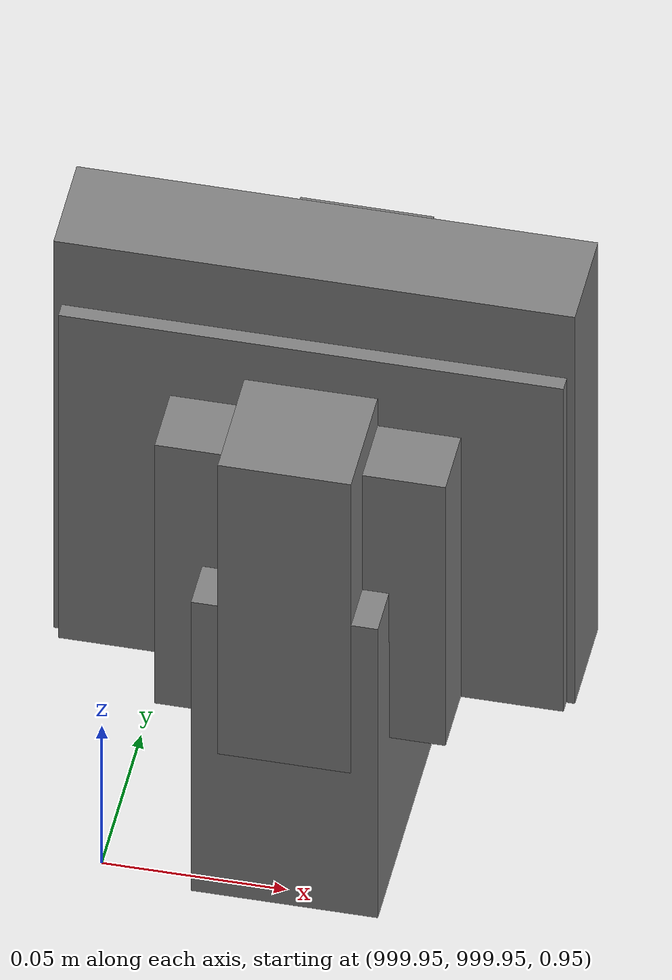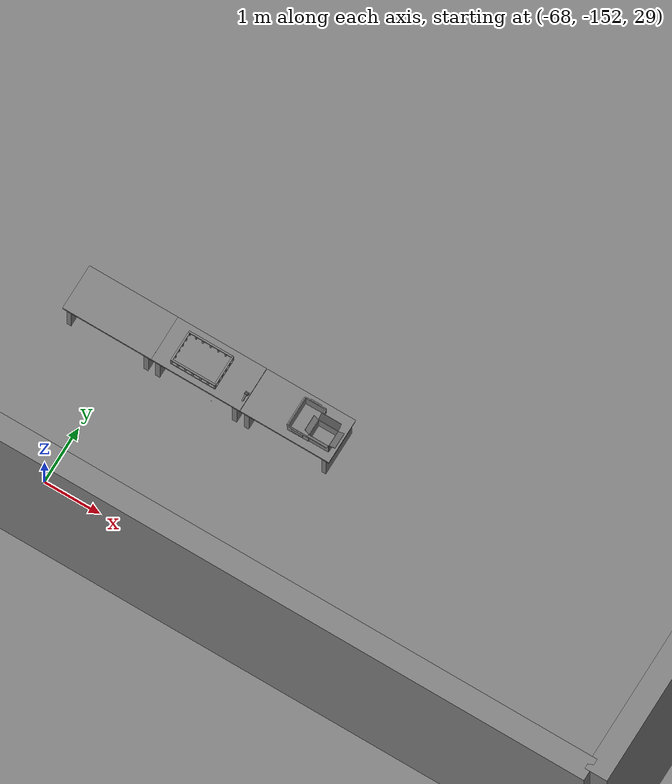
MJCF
<mujoco>
    <option gravity="0.000000000 0.000000000 -9.810000420" timestep="0.0049999999" integrator="implicitfast" density="1.225" viscosity="1.8000001e-05" noslip_iterations="10" iterations="100" sdf_iterations="50">
        <flag multiccd="disable"/>
    </option>
    <size memory="1000M"/>
    <compiler coordinate="local"/>
    <worldbody>
        <light cutoff="30" pos="0 1 1" dir="0 -1 -2"/>
        <light cutoff="30" pos="0 -1 1" dir="0 1 -2"/>
        <body pos="1000.000000000 1000.000000000 1.000000000" euler="0.000000000 0.000000000 180.000000000" name="openloong_gripper_2f85_fix_base_usda_battery_01">
            <geom contype="1" conaffinity="1" density="1000" type="box" material="" rgba="0.500000000 0.500000000 0.500000000 1.000000000" solimp="0.899999976 0.949999988 0.001000000" friction="1.000000000 0.005000000 0.000100000" solref="0.020000000 1.000000000" margin="0" condim="3" group="0" pos="-0.011123657 -0.041940309 0.101691343" quat="1.000000000 0.000000000 0.000000000 0.000000000" size="0.010800000 0.003375000 0.004725000" name="openloong_gripper_2f85_fix_base_usda_geom_29FC075F_102A_4480_B4A5_0B7F25FAA29F"/>
            <geom contype="1" conaffinity="1" density="1000" type="box" material="" rgba="0.500000000 0.500000000 0.500000000 1.000000000" solimp="0.899999976 0.949999988 0.001000000" friction="1.000000000 0.005000000 0.000100000" solref="0.020000000 1.000000000" margin="0" condim="3" group="0" pos="-0.010876465 -0.044247437 0.047066893" quat="0.998702705 -0.050920475 0.000000000 0.000000000" size="0.009450001 0.002700000 0.024975000" name="openloong_gripper_2f85_fix_base_usda_geom_0BAF0F5B_BD3E_42EC_85F4_A452B4F6267B"/>
            <geom contype="1" conaffinity="1" density="1000" type="box" material="" rgba="0.500000000 0.500000000 0.500000000 1.000000000" solimp="0.899999976 0.949999988 0.001000000" friction="1.000000000 0.005000000 0.000100000" solref="0.020000000 1.000000000" margin="0" condim="3" group="0" pos="-0.001235962 -0.000659180 0.047381196" quat="1.000000000 0.000000000 0.000000000 0.000000000" size="0.039420001 0.039150000 0.047250003" name="openloong_gripper_2f85_fix_base_usda_geom_9DD1E4B0_34C2_4BE0_9480_ADB82B972F42"/>
            <geom contype="1" conaffinity="1" density="1000" type="box" material="" rgba="0.500000000 0.500000000 0.500000000 1.000000000" solimp="0.899999976 0.949999988 0.001000000" friction="1.000000000 0.005000000 0.000100000" solref="0.020000000 1.000000000" margin="0" condim="3" group="0" pos="-0.010876465 -0.039138794 0.009851727" quat="1.000000000 0.000000000 0.000000000 0.000000000" size="0.009450001 0.010800000 0.013500000" name="openloong_gripper_2f85_fix_base_usda_geom_40E48D30_50C6_44C8_90A8_58CD7433C97C"/>
            <geom contype="1" conaffinity="1" density="1000" type="box" material="" rgba="0.500000000 0.500000000 0.500000000 1.000000000" solimp="0.899999976 0.949999988 0.001000000" friction="1.000000000 0.005000000 0.000100000" solref="0.020000000 1.000000000" margin="0" condim="3" group="0" pos="-0.010876465 -0.041528322 0.071508206" quat="1.000000000 0.000000000 0.000000000 0.000000000" size="0.009450001 0.002700000 0.027000001" name="openloong_gripper_2f85_fix_base_usda_geom_169A2635_17DB_4676_A965_2922BDC70A36"/>
            <freejoint name="openloong_gripper_2f85_fix_base_usda_battery_01_joint"/>
            <site size="0.005000000 0.005000000 0.005000000" rgba="0.500000000 0.500000000 0.500000000 1.000000000" pos="0.000000000 0.000000000 0.000000000" quat="0.999961913 0.008726500 0.000000000 0.000000000" group="0" type="sphere" name="openloong_gripper_2f85_fix_base_usda_battery_01site"/>
        </body>
        <body pos="-66.361663818 -149.157989502 31.164411545" euler="1.586280704 -23.113754272 136.321197510" mocap="true" name="spotlight3_SpotLight"/>
        <body pos="1000.000000000 1000.000000000 1.000000000" euler="0.000000000 0.000000000 180.000000000" name="openloong_gripper_2f85_fix_base_usda_cpu_fan">
            <geom contype="1" conaffinity="1" density="1000" type="box" material="" rgba="0.500000000 0.500000000 0.500000000 1.000000000" solimp="0.899999976 0.949999988 0.001000000" friction="1.000000000 0.005000000 0.000100000" solref="0.020000000 1.000000000" margin="0" condim="3" group="0" pos="0.000000000 0.000000000 0.070034981" quat="0.000000000 0.000000000 0.000000000 1.000000000" size="0.070700005 0.014699999 0.070700005" name="openloong_gripper_2f85_fix_base_usda_geom_7D55D244_EA14_4BAE_BEDA_CB2C4E8FD00D"/>
            <freejoint name="openloong_gripper_2f85_fix_base_usda_cpu_fan_joint"/>
            <site size="0.005000000 0.005000000 0.005000000" rgba="0.500000000 0.500000000 0.500000000 1.000000000" pos="0.000000000 0.000000000 0.000000000" quat="0.999961913 0.008726535 0.000000000 0.000000000" group="0" type="sphere" name="openloong_gripper_2f85_fix_base_usda_cpu_fancsite"/>
        </body>
        <body pos="1000.000000000 1000.000000000 1.000000000" euler="0.000000000 0.000000000 180.000000000" name="openloong_gripper_2f85_fix_base_usda_wifi_box">
            <geom contype="1" conaffinity="1" density="1000" type="box" material="" rgba="0.500000000 0.500000000 0.500000000 1.000000000" solimp="0.899999976 0.949999988 0.001000000" friction="1.000000000 0.005000000 0.000100000" solref="0.020000000 1.000000000" margin="0" condim="3" group="0" pos="0.000000000 0.000000000 0.058978677" quat="0.000000000 0.000000047 0.000000000 1.000000000" size="0.068499997 0.018999999 0.059000000" name="openloong_gripper_2f85_fix_base_usda_geom_077571CF_E836_4696_9C05_A14A22AB0100"/>
            <freejoint name="openloong_gripper_2f85_fix_base_usda_wifi_box_joint"/>
            <site size="0.005000000 0.005000000 0.005000000" rgba="0.500000000 0.500000000 0.500000000 1.000000000" pos="0.000000000 0.000000000 0.000000000" quat="0.999961913 0.008726500 0.000000000 0.000000000" group="0" type="sphere" name="openloong_gripper_2f85_fix_base_usda_wifi_boxsite"/>
        </body>
        <body pos="1000.000000000 1000.000000000 1.000000000" euler="0.000011953 0.000005123 -179.999984741" name="openloong_gripper_2f85_fix_base_usda_intel_box">
            <geom contype="1" conaffinity="1" density="1000" type="box" material="" rgba="0.500000000 0.500000000 0.500000000 1.000000000" solimp="0.899999976 0.949999988 0.001000000" friction="1.000000000 0.005000000 0.000100000" solref="0.020000000 1.000000000" margin="0" condim="3" group="0" pos="0.000000000 -0.000067139 0.000082284" quat="0.707106709 0.000000225 0.000000253 0.707106650" size="0.052800003 0.025300000 0.052800003" name="openloong_gripper_2f85_fix_base_usda_geom_B904AA2D_099C_4865_9CAB_F0DC513C6463"/>
            <freejoint name="openloong_gripper_2f85_fix_base_usda_intel_box_joint"/>
            <site size="0.005000000 0.005000000 0.005000000" rgba="0.500000000 0.500000000 0.500000000 1.000000000" pos="0.000000000 0.000000000 0.000000000" quat="0.999961913 0.008726500 0.000000000 0.000000000" group="0" type="sphere" name="openloong_gripper_2f85_fix_base_usda_intel_boxsite"/>
        </body>
        <body pos="-66.180679321 -149.778015137 31.166332245" euler="-25.648809433 34.812355042 32.934417725" mocap="true" name="spotlight5_SpotLight"/>
        <body pos="1000.000000000 999.999938965 1.000000000" euler="0.000000000 0.000000000 180.000000000" name="openloong_gripper_2f85_fix_base_usda_intelcore_i5">
            <geom contype="1" conaffinity="1" density="1000" type="box" material="" rgba="0.500000000 0.500000000 0.500000000 1.000000000" solimp="0.899999976 0.949999988 0.001000000" friction="1.000000000 0.005000000 0.000100000" solref="0.020000000 1.000000000" margin="0" condim="3" group="0" pos="0.000000000 0.000000000 0.051722717" quat="0.707106709 0.000000000 0.000000000 -0.707106769" size="0.052800000 0.018080002 0.052800000" name="openloong_gripper_2f85_fix_base_usda_geom_0B633D05_255F_478C_B45D_7E2FDE8FBF90"/>
            <freejoint name="openloong_gripper_2f85_fix_base_usda_intelcore_i5_joint"/>
            <site size="0.005000000 0.005000000 0.005000000" rgba="0.500000000 0.500000000 0.500000000 1.000000000" pos="0.000000000 0.000000000 0.000000000" quat="0.999961913 0.008726534 0.000000000 0.000000000" group="0" type="sphere" name="openloong_gripper_2f85_fix_base_usda_intelcore_i5site"/>
        </body>
        <body pos="-66.320228577 -149.424468994 31.162549973" euler="-64.258399963 2.017166138 167.687438965" mocap="true" name="spotlight1_SpotLight"/>
        <body pos="-64.866622925 -149.383972168 30.183746338" euler="89.999984741 89.999946594 0.000000000" name="openloong_gripper_2f85_fix_base_usda_bluebox_01">
            <geom contype="1" conaffinity="1" density="1000" type="box" material="" rgba="0.500000000 0.500000000 0.500000000 1.000000000" solimp="0.899999976 0.949999988 0.001000000" friction="1.000000000 0.005000000 0.000100000" solref="0.020000000 1.000000000" margin="0" condim="3" group="0" pos="0.276580811 0.187225342 0.000068665" quat="0.707106948 0.000077471 0.707106352 0.000077486" size="0.100000001 0.057999998 0.010000000" name="openloong_gripper_2f85_fix_base_usda_geom_060F8B1A_6205_443A_AAF2_9DFD1FCC6079"/>
            <geom contype="1" conaffinity="1" density="1000" type="box" material="" rgba="0.500000000 0.500000000 0.500000000 1.000000000" solimp="0.899999976 0.949999988 0.001000000" friction="1.000000000 0.005000000 0.000100000" solref="0.020000000 1.000000000" margin="0" condim="3" group="0" pos="0.000000000 0.002883911 0.000000000" quat="0.999999881 0.000000000 0.000000000 0.000000000" size="0.254000008 0.003000000 0.172000006" name="openloong_gripper_2f85_fix_base_usda_geom_9B9C3D61_D73E_4682_9AB2_0F91E8EFDCC8"/>
            <geom contype="1" conaffinity="1" density="1000" type="box" material="" rgba="0.500000000 0.500000000 0.500000000 1.000000000" solimp="0.899999976 0.949999988 0.001000000" friction="1.000000000 0.005000000 0.000100000" solref="0.020000000 1.000000000" margin="0" condim="3" group="0" pos="0.000000000 0.124874115 0.173484802" quat="0.999796331 0.020176515 -0.000000015 0.000000030" size="0.259999990 0.119999997 0.007000000" name="openloong_gripper_2f85_fix_base_usda_geom_BA4058DF_FCF3_4994_82E0_6301AB51EF7D"/>
            <geom contype="1" conaffinity="1" density="1000" type="box" material="" rgba="0.500000000 0.500000000 0.500000000 1.000000000" solimp="0.899999976 0.949999988 0.001000000" friction="1.000000000 0.005000000 0.000100000" solref="0.020000000 1.000000000" margin="0" condim="3" group="0" pos="0.000000000 0.124874115 -0.173469543" quat="0.999796331 -0.020176545 -0.000000015 0.000000000" size="0.259999990 0.119999997 0.007000000" name="openloong_gripper_2f85_fix_base_usda_geom_08BEDC9F_67B7_4B50_A9B8_DF9ECCCFBB5C"/>
            <geom contype="1" conaffinity="1" density="1000" type="box" material="" rgba="0.500000000 0.500000000 0.500000000 1.000000000" solimp="0.899999976 0.949999988 0.001000000" friction="1.000000000 0.005000000 0.000100000" solref="0.020000000 1.000000000" margin="0" condim="3" group="0" pos="0.000000000 0.214008331 0.188980103" quat="0.999912977 0.013176724 0.000000015 0.000000000" size="0.259999990 0.029999999 0.012500000" name="openloong_gripper_2f85_fix_base_usda_geom_09496D20_BAC3_4E44_94CF_50C41EEF6027"/>
            <geom contype="1" conaffinity="1" density="1000" type="box" material="" rgba="0.500000000 0.500000000 0.500000000 1.000000000" solimp="0.899999976 0.949999988 0.001000000" friction="1.000000000 0.005000000 0.000100000" solref="0.020000000 1.000000000" margin="0" condim="3" group="0" pos="-0.258361816 0.125289917 0.001876831" quat="0.702796936 -0.020792112 0.710783124 0.020769298" size="0.189999998 0.119999997 0.009000000" name="openloong_gripper_2f85_fix_base_usda_geom_323E4C11_AACB_4FFF_AA74_178950C1BF47"/>
            <geom contype="1" conaffinity="1" density="1000" type="box" material="" rgba="0.500000000 0.500000000 0.500000000 1.000000000" solimp="0.899999976 0.949999988 0.001000000" friction="1.000000000 0.005000000 0.000100000" solref="0.020000000 1.000000000" margin="0" condim="3" group="0" pos="0.000000000 0.214008331 -0.188980103" quat="0.999912977 -0.013176769 0.000000030 0.000000015" size="0.259999990 0.029999999 0.012500000" name="openloong_gripper_2f85_fix_base_usda_geom_33A73BD5_FD88_4B67_925B_D90391E5E294"/>
            <geom contype="1" conaffinity="1" density="1000" type="box" material="" rgba="0.500000000 0.500000000 0.500000000 1.000000000" solimp="0.899999976 0.949999988 0.001000000" friction="1.000000000 0.005000000 0.000100000" solref="0.020000000 1.000000000" margin="0" condim="3" group="0" pos="-0.276611328 0.187225342 0.000068665" quat="0.707106650 0.000077441 0.707106709 0.000077456" size="0.100000001 0.057999998 0.010000000" name="openloong_gripper_2f85_fix_base_usda_geom_692807E6_0688_4A63_B286_D8DD2A9BC6FE"/>
            <geom contype="1" conaffinity="1" density="1000" type="box" material="" rgba="0.500000000 0.500000000 0.500000000 1.000000000" solimp="0.899999976 0.949999988 0.001000000" friction="1.000000000 0.005000000 0.000100000" solref="0.020000000 1.000000000" margin="0" condim="3" group="0" pos="0.258331299 0.125289917 0.001876831" quat="0.702851415 0.018856421 0.710823774 -0.019329369" size="0.189999998 0.119999997 0.009000000" name="openloong_gripper_2f85_fix_base_usda_geom_51AE3D60_8DEC_4758_A4BD_FC6FC24AF3A0"/>
            <freejoint name="openloong_gripper_2f85_fix_base_usda_bluebox_01_joint"/>
            <site size="0.005000000 0.005000000 0.005000000" rgba="0.500000000 0.500000000 0.500000000 1.000000000" pos="0.000000000 0.000000000 0.000000000" quat="0.999961913 0.008726534 0.000000000 0.000000000" group="0" type="sphere" name="openloong_gripper_2f85_fix_base_usda_bluebox_01site"/>
        </body>
        <body pos="-64.496299744 -149.491867065 30.235729218" euler="0.000000000 0.000000000 89.999946594" name="openloong_gripper_2f85_fix_base_usda_cardboardbox_01">
            <geom contype="1" conaffinity="1" density="1000" type="box" material="" rgba="0.500000000 0.500000000 0.500000000 1.000000000" solimp="0.899999976 0.949999988 0.001000000" friction="1.000000000 0.005000000 0.000100000" solref="0.020000000 1.000000000" margin="0" condim="3" group="0" pos="-0.003166199 -0.004086494 0.005052090" quat="1.000000000 0.000000000 0.000000000 0.000000000" size="0.142499998 0.177500010 0.005000000" name="openloong_gripper_2f85_fix_base_usda_geom_C33044AD_2AEC_4EFA_B787_A409A475F406"/>
            <geom contype="1" conaffinity="1" density="1000" type="box" material="" rgba="0.500000000 0.500000000 0.500000000 1.000000000" solimp="0.899999976 0.949999988 0.001000000" friction="1.000000000 0.005000000 0.000100000" solref="0.020000000 1.000000000" margin="0" condim="3" group="0" pos="-0.003166199 0.170316696 0.150570869" quat="1.000000000 0.000000000 0.000000000 0.000000000" size="0.142499998 0.005000000 0.149999991" name="openloong_gripper_2f85_fix_base_usda_geom_DA2E5D13_FDF9_48FD_8A35_8726D0701F11"/>
            <geom contype="1" conaffinity="1" density="1000" type="box" material="" rgba="0.500000000 0.500000000 0.500000000 1.000000000" solimp="0.899999976 0.949999988 0.001000000" friction="1.000000000 0.005000000 0.000100000" solref="0.020000000 1.000000000" margin="0" condim="3" group="0" pos="-0.147399902 -0.005307198 0.150570869" quat="1.000000000 0.000000000 0.000000000 0.000000000" size="0.005000000 0.177500010 0.149999991" name="openloong_gripper_2f85_fix_base_usda_geom_463BA96D_8B52_46B9_A399_E0A25B6081C0"/>
            <geom contype="1" conaffinity="1" density="1000" type="box" material="" rgba="0.500000000 0.500000000 0.500000000 1.000000000" solimp="0.899999976 0.949999988 0.001000000" friction="1.000000000 0.005000000 0.000100000" solref="0.020000000 1.000000000" margin="0" condim="3" group="0" pos="0.140275955 -0.005307198 0.150570869" quat="1.000000000 0.000000000 0.000000000 0.000000000" size="0.005000000 0.177500010 0.149999991" name="openloong_gripper_2f85_fix_base_usda_geom_C19589CD_8F3C_4550_9F80_AB1ACF0E0860"/>
            <geom contype="1" conaffinity="1" density="1000" type="box" material="" rgba="0.500000000 0.500000000 0.500000000 1.000000000" solimp="0.899999976 0.949999988 0.001000000" friction="1.000000000 0.005000000 0.000100000" solref="0.020000000 1.000000000" margin="0" condim="3" group="0" pos="-0.003166199 -0.181550980 0.150570869" quat="1.000000000 0.000000000 0.000000000 0.000000000" size="0.142499998 0.005000000 0.149999991" name="openloong_gripper_2f85_fix_base_usda_geom_8CEE30EB_FD0E_4ABB_8F18_89603789433F"/>
            <freejoint name="openloong_gripper_2f85_fix_base_usda_cardboardbox_01_joint"/>
            <site size="0.005000000 0.005000000 0.005000000" rgba="0.500000000 0.500000000 0.500000000 1.000000000" pos="0.000000000 0.000000000 0.000000000" quat="0.999961913 0.008726535 0.000000000 0.000000000" group="0" type="sphere" name="openloong_gripper_2f85_fix_base_usda_site_DDF96DF2_EC0C_46A2_93AC_20AC8E15EA7A"/>
            <body pos="0.139160156 -0.004048347 0.301930904" euler="-179.999954224 49.383502960 179.999954224" name="openloong_gripper_2f85_fix_base_usda_A1_006">
                <geom contype="1" conaffinity="1" density="1000" type="box" material="" rgba="0.500000000 0.500000000 0.500000000 1.000000000" solimp="0.899999976 0.949999988 0.001000000" friction="1.000000000 0.005000000 0.000100000" solref="0.020000000 1.000000000" margin="0" condim="3" group="0" pos="-0.071587563 0.000009537 0.001745224" quat="0.999999881 0.000000000 0.000000000 0.000000000" size="0.071249999 0.179999992 0.002500000" name="openloong_gripper_2f85_fix_base_usda_geom_9D9F3FF2_5A6C_47D8_AEFE_0917F0FCF59D"/>
                <joint armature="0" stiffness="0.07" damping="0.0099999998" axis="0.000000 1.000000 0.000000" type="hinge" name="openloong_gripper_2f85_fix_base_usda_A1_006"/>
            </body>
            <body pos="-0.145902634 -0.004086494 0.301938057" euler="-180.000000000 -60.000011444 -180.000000000" name="openloong_gripper_2f85_fix_base_usda_A2_006">
                <geom contype="1" conaffinity="1" density="1000" type="box" material="" rgba="0.500000000 0.500000000 0.500000000 1.000000000" solimp="0.899999976 0.949999988 0.001000000" friction="1.000000000 0.005000000 0.000100000" solref="0.020000000 1.000000000" margin="0" condim="3" group="0" pos="0.071268082 0.000009537 0.002717972" quat="0.000002921 0.000000000 -0.000000030 0.999999881" size="0.071249999 0.179999992 0.002500000" name="openloong_gripper_2f85_fix_base_usda_geom_60DB23BC_B3D9_4B08_8692_B4905CAE73AA"/>
                <joint armature="0" stiffness="0.07" damping="0.0099999998" axis="0.000000 1.000000 0.000000" type="hinge" name="openloong_gripper_2f85_fix_base_usda_A2_006"/>
            </body>
            <body pos="-0.003385544 0.175991058 0.301930904" euler="-125.858116150 -0.000004561 0.000002331" name="openloong_gripper_2f85_fix_base_usda_B2_006">
                <geom contype="1" conaffinity="1" density="1000" type="box" material="" rgba="0.500000000 0.500000000 0.500000000 1.000000000" solimp="0.899999976 0.949999988 0.001000000" friction="1.000000000 0.005000000 0.000100000" solref="0.020000000 1.000000000" margin="0" condim="3" group="0" pos="0.000009537 -0.070939064 -0.002470016" quat="0.999614120 0.027776197 -0.000000015 0.000000030" size="0.137500003 0.064999998 0.005000000" name="openloong_gripper_2f85_fix_base_usda_geom_74023A42_D028_4DFF_B411_B1D22C43DDF3"/>
                <joint armature="0" stiffness="0.07" damping="0.0099999998" axis="1.000000 0.000000 0.000000" type="hinge" name="openloong_gripper_2f85_fix_base_usda_B2_006"/>
            </body>
            <body pos="-0.003385544 -0.184140205 0.301938057" euler="147.805557251 0.000000000 0.000000000" name="openloong_gripper_2f85_fix_base_usda_B1_006">
                <geom contype="1" conaffinity="1" density="1000" type="box" material="" rgba="0.500000000 0.500000000 0.500000000 1.000000000" solimp="0.899999976 0.949999988 0.001000000" friction="1.000000000 0.005000000 0.000100000" solref="0.020000000 1.000000000" margin="0" condim="3" group="0" pos="-0.000028610 0.070202351 -0.002703667" quat="0.999614179 -0.027776167 0.000000000 0.000000000" size="0.137500003 0.064999998 0.005000000" name="openloong_gripper_2f85_fix_base_usda_geom_C678D2B3_17A9_48E9_B51B_904A0EF34E3A"/>
                <joint armature="0" stiffness="0.07" damping="0.0099999998" axis="1.000000 0.000000 0.000000" type="hinge" name="openloong_gripper_2f85_fix_base_usda_B1_006"/>
            </body>
        </body>
        <body pos="-65.882858276 -149.481979370 30.229999542" euler="-64.487716675 0.000000000 0.000000000" name="openloong_gripper_2f85_fix_base_usda_Barcode">
            <geom contype="1" conaffinity="1" density="1000" type="box" material="" rgba="0.500000000 0.500000000 0.500000000 1.000000000" solimp="0.899999976 0.949999988 0.001000000" friction="1.000000000 0.005000000 0.000100000" solref="0.020000000 1.000000000" margin="0" condim="3" group="0" pos="0.000000000 0.013038635 0.001419067" quat="0.000000000 0.000000000 0.000000000 1.000000119" size="0.034000002 0.010000000 0.017999999" name="openloong_gripper_2f85_fix_base_usda_geom_11F2CA8A_9585_4E4F_9C73_198188659213"/>
            <geom contype="1" conaffinity="1" density="1000" type="box" material="" rgba="0.500000000 0.500000000 0.500000000 1.000000000" solimp="0.899999976 0.949999988 0.001000000" friction="1.000000000 0.005000000 0.000100000" solref="0.020000000 1.000000000" margin="0" condim="3" group="0" pos="0.000000000 -0.035301208 -0.007095337" quat="0.000000000 0.000000000 -0.043619365 0.999048233" size="0.028999999 0.010000000 0.020000000" name="openloong_gripper_2f85_fix_base_usda_geom_954F7C60_6195_48CE_B0B7_15F3D5257AB3"/>
            <geom contype="1" conaffinity="1" density="1000" type="box" material="" rgba="0.500000000 0.500000000 0.500000000 1.000000000" solimp="0.899999976 0.949999988 0.001000000" friction="1.000000000 0.005000000 0.000100000" solref="0.020000000 1.000000000" margin="0" condim="3" group="0" pos="0.000000000 -0.043411255 -0.011749268" quat="0.922262907 0.386563420 0.000000000 0.000000000" size="0.026000001 0.010000000 0.020000000" name="openloong_gripper_2f85_fix_base_usda_geom_A046E566_6877_4CFF_90B7_CE2D00783D90"/>
            <geom contype="1" conaffinity="1" density="1000" type="box" material="" rgba="0.500000000 0.500000000 0.500000000 1.000000000" solimp="0.899999976 0.949999988 0.001000000" friction="1.000000000 0.005000000 0.000100000" solref="0.020000000 1.000000000" margin="0" condim="3" group="0" pos="0.000000000 -0.016967773 -0.031860352" quat="0.000000000 0.000000000 0.000000000 1.000000119" size="0.008000000 0.010000000 0.013000000" name="openloong_gripper_2f85_fix_base_usda_geom_7C7ACB6C_A3F5_40F2_9C2E_C8D7A524839D"/>
            <geom contype="1" conaffinity="1" density="1000" type="box" material="" rgba="0.500000000 0.500000000 0.500000000 1.000000000" solimp="0.899999976 0.949999988 0.001000000" friction="1.000000000 0.005000000 0.000100000" solref="0.020000000 1.000000000" margin="0" condim="3" group="0" pos="0.000000000 -0.001869202 0.000312805" quat="0.953716993 0.300705761 0.000000000 0.000000000" size="0.032000002 0.010000000 0.018999999" name="openloong_gripper_2f85_fix_base_usda_geom_494F52E0_5041_4E1D_9D53_99B3B0AE9836"/>
            <geom contype="1" conaffinity="1" density="1000" type="box" material="" rgba="0.500000000 0.500000000 0.500000000 1.000000000" solimp="0.899999976 0.949999988 0.001000000" friction="1.000000000 0.005000000 0.000100000" solref="0.020000000 1.000000000" margin="0" condim="3" group="0" pos="0.000000000 -0.019531250 -0.003173828" quat="0.953716993 0.300705761 0.000000000 0.000000000" size="0.030999999 0.010000000 0.020000000" name="openloong_gripper_2f85_fix_base_usda_geom_D0FF38AE_65C5_4F3A_B98A_248E4277C5A2"/>
            <geom contype="1" conaffinity="1" density="1000" type="box" material="" rgba="0.500000000 0.500000000 0.500000000 1.000000000" solimp="0.899999976 0.949999988 0.001000000" friction="1.000000000 0.005000000 0.000100000" solref="0.020000000 1.000000000" margin="0" condim="3" group="0" pos="0.000000000 -0.035301208 -0.007095337" quat="0.953716993 0.300705761 0.000000000 0.000000000" size="0.028999999 0.010000000 0.020000000" name="openloong_gripper_2f85_fix_base_usda_geom_97D71376_7A5F_481D_A8C2_A210899E6A96"/>
            <geom contype="1" conaffinity="1" density="1000" type="box" material="" rgba="0.500000000 0.500000000 0.500000000 1.000000000" solimp="0.899999976 0.949999988 0.001000000" friction="1.000000000 0.005000000 0.000100000" solref="0.020000000 1.000000000" margin="0" condim="3" group="0" pos="0.000000000 -0.042617798 -0.071121216" quat="0.000000000 0.000000000 0.000000000 1.000000119" size="0.013000000 0.021000000 0.059999999" name="openloong_gripper_2f85_fix_base_usda_geom_16C33542_779B_434E_A5EB_D6D53EB4F635"/>
            <freejoint name="openloong_gripper_2f85_fix_base_usda_Barcode_joint"/>
            <site size="0.005000000 0.005000000 0.005000000" rgba="0.500000000 0.500000000 0.500000000 1.000000000" pos="0.000000000 0.000000000 0.000000000" quat="1.000000000 0.000000000 0.000000000 0.000000000" group="0" type="sphere" name="openloong_gripper_2f85_fix_base_usda_Barcode_site"/>
        </body>
        <body pos="-66.745018005 -149.392349243 30.184000015" euler="0.000000000 0.000000000 89.999946594" name="[22332238385265]_Basket_01">
            <geom contype="1" conaffinity="1" density="1000" type="box" material="" rgba="0.500000000 0.500000000 0.500000000 1.000000000" solimp="0.899999976 0.949999988 0.001000000" friction="1.000000000 0.005000000 0.000100000" solref="0.020000000 1.000000000" margin="0" condim="3" group="0" pos="-0.052425385 0.389207840 0.089787483" quat="0.707107008 0.000000000 0.000000000 0.707106411" size="0.014249999 0.014249999 0.059999999" name="[22332238385265]_geom_4C36C946_7059_4022_9679_2C291EF1626C"/>
            <geom contype="1" conaffinity="1" density="1000" type="box" material="" rgba="0.500000000 0.500000000 0.500000000 1.000000000" solimp="0.899999976 0.949999988 0.001000000" friction="1.000000000 0.005000000 0.000100000" solref="0.020000000 1.000000000" margin="0" condim="3" group="0" pos="0.264015198 -0.133043289 0.089787483" quat="0.707107008 0.000000000 0.000000000 0.707106411" size="0.014249999 0.014249999 0.059999999" name="[22332238385265]_geom_DF90800D_5CB5_446F_AF56_F20ADEB88A73"/>
            <geom contype="1" conaffinity="1" density="1000" type="box" material="" rgba="0.500000000 0.500000000 0.500000000 1.000000000" solimp="0.899999976 0.949999988 0.001000000" friction="1.000000000 0.005000000 0.000100000" solref="0.020000000 1.000000000" margin="0" condim="3" group="0" pos="-0.264015198 -0.265548706 0.089793205" quat="0.707107008 0.000000000 0.000000000 0.707106411" size="0.014249999 0.014249999 0.059999999" name="[22332238385265]_geom_9E76D389_F32B_40E9_9262_26E153A44AB3"/>
            <geom contype="1" conaffinity="1" density="1000" type="box" material="" rgba="0.500000000 0.500000000 0.500000000 1.000000000" solimp="0.899999976 0.949999988 0.001000000" friction="1.000000000 0.005000000 0.000100000" solref="0.020000000 1.000000000" margin="0" condim="3" group="0" pos="-0.160263062 -0.389322281 0.089793205" quat="0.707107008 0.000000000 0.000000000 0.707106411" size="0.014249999 0.014249999 0.059999999" name="[22332238385265]_geom_2164A8D7_1202_416F_834E_FFFB46E4DB75"/>
            <geom contype="1" conaffinity="1" density="1000" type="box" material="" rgba="0.500000000 0.500000000 0.500000000 1.000000000" solimp="0.899999976 0.949999988 0.001000000" friction="1.000000000 0.005000000 0.000100000" solref="0.020000000 1.000000000" margin="0" condim="3" group="0" pos="0.162265778 -0.389322281 0.089787483" quat="0.707107008 0.000000000 0.000000000 0.707106411" size="0.014249999 0.014249999 0.059999999" name="[22332238385265]_geom_F9981B7A_70A4_4BBC_901B_4C6AC8C9BACE"/>
            <geom contype="1" conaffinity="1" density="1000" type="box" material="" rgba="0.500000000 0.500000000 0.500000000 1.000000000" solimp="0.899999976 0.949999988 0.001000000" friction="1.000000000 0.005000000 0.000100000" solref="0.020000000 1.000000000" margin="0" condim="3" group="0" pos="0.264015198 0.389207840 0.089787483" quat="0.707107008 0.000000000 0.000000000 0.707106411" size="0.014249999 0.014249999 0.059999999" name="[22332238385265]_geom_567E2ABA_C055_4366_9584_9049913B01EF"/>
            <geom contype="1" conaffinity="1" density="1000" type="box" material="" rgba="0.500000000 0.500000000 0.500000000 1.000000000" solimp="0.899999976 0.949999988 0.001000000" friction="1.000000000 0.005000000 0.000100000" solref="0.020000000 1.000000000" margin="0" condim="3" group="0" pos="-0.264015198 -0.133043289 0.089793205" quat="0.707107008 0.000000000 0.000000000 0.707106411" size="0.014249999 0.014249999 0.059999999" name="[22332238385265]_geom_1D2810AA_F434_4CE1_9033_328728EAA970"/>
            <geom contype="1" conaffinity="1" density="1000" type="box" material="" rgba="0.500000000 0.500000000 0.500000000 1.000000000" solimp="0.899999976 0.949999988 0.001000000" friction="1.000000000 0.005000000 0.000100000" solref="0.020000000 1.000000000" margin="0" condim="3" group="0" pos="-0.264026642 0.269256592 0.089793205" quat="0.707107008 0.000000000 0.000000000 0.707106411" size="0.014249999 0.014249999 0.059999999" name="[22332238385265]_geom_5CADC92D_000F_4728_8C79_D7859D3080E5"/>
            <geom contype="1" conaffinity="1" density="1000" type="box" material="" rgba="0.500000000 0.500000000 0.500000000 1.000000000" solimp="0.899999976 0.949999988 0.001000000" friction="1.000000000 0.005000000 0.000100000" solref="0.020000000 1.000000000" margin="0" condim="3" group="0" pos="0.054462433 0.389207840 0.089787483" quat="0.707107008 0.000000000 0.000000000 0.707106411" size="0.014249999 0.014249999 0.059999999" name="[22332238385265]_geom_CD872840_20B9_484E_A5F7_995334BC1DB6"/>
            <geom contype="1" conaffinity="1" density="1000" type="box" material="" rgba="0.500000000 0.500000000 0.500000000 1.000000000" solimp="0.899999976 0.949999988 0.001000000" friction="1.000000000 0.005000000 0.000100000" solref="0.020000000 1.000000000" margin="0" condim="3" group="0" pos="0.054462433 -0.389322281 0.089787483" quat="0.707107008 0.000000000 0.000000000 0.707106411" size="0.014249999 0.014249999 0.059999999" name="[22332238385265]_geom_08244A24_727A_4A5B_BD7A_86BEFEF49412"/>
            <geom contype="1" conaffinity="1" density="1000" type="box" material="" rgba="0.500000000 0.500000000 0.500000000 1.000000000" solimp="0.899999976 0.949999988 0.001000000" friction="1.000000000 0.005000000 0.000100000" solref="0.020000000 1.000000000" margin="0" condim="3" group="0" pos="0.264015198 0.269256592 0.089793205" quat="0.707107008 0.000000000 0.000000000 0.707106411" size="0.014249999 0.014249999 0.059999999" name="[22332238385265]_geom_249890A6_BC17_44A5_BCA9_5D1BC7AB8BCD"/>
            <geom contype="1" conaffinity="1" density="1000" type="box" material="" rgba="0.500000000 0.500000000 0.500000000 1.000000000" solimp="0.899999976 0.949999988 0.001000000" friction="1.000000000 0.005000000 0.000100000" solref="0.020000000 1.000000000" margin="0" condim="3" group="0" pos="0.264015198 -0.389322281 0.089787483" quat="0.707107008 0.000000000 0.000000000 0.707106411" size="0.014249999 0.014249999 0.059999999" name="[22332238385265]_geom_0E540431_1F6F_454A_874E_E7F656708C72"/>
            <geom contype="1" conaffinity="1" density="1000" type="box" material="" rgba="0.500000000 0.500000000 0.500000000 1.000000000" solimp="0.899999976 0.949999988 0.001000000" friction="1.000000000 0.005000000 0.000100000" solref="0.020000000 1.000000000" margin="0" condim="3" group="0" pos="0.000000000 0.000000000 0.015998840" quat="0.707107008 0.000000000 0.000000000 0.707106411" size="0.403499991 0.279000014 0.015750000" name="[22332238385265]_geom_84A6D79E_5724_41F0_BDF1_42DE8BB5A320"/>
            <geom contype="1" conaffinity="1" density="1000" type="box" material="" rgba="0.500000000 0.500000000 0.500000000 1.000000000" solimp="0.899999976 0.949999988 0.001000000" friction="1.000000000 0.005000000 0.000100000" solref="0.020000000 1.000000000" margin="0" condim="3" group="0" pos="0.000000000 -0.389476776 0.163619041" quat="0.707107008 0.000000000 0.000000000 0.707106411" size="0.015000000 0.277500004 0.015750000" name="[22332238385265]_geom_ADCAE1AE_0055_4454_AD0E_7F5B6A1656F7"/>
            <geom contype="1" conaffinity="1" density="1000" type="box" material="" rgba="0.500000000 0.500000000 0.500000000 1.000000000" solimp="0.899999976 0.949999988 0.001000000" friction="1.000000000 0.005000000 0.000100000" solref="0.020000000 1.000000000" margin="0" condim="3" group="0" pos="0.162265778 0.389207840 0.089787483" quat="0.707107008 0.000000000 0.000000000 0.707106411" size="0.014249999 0.014249999 0.059999999" name="[22332238385265]_geom_9A10E778_FD09_45CD_A639_EC6E98B3203B"/>
            <geom contype="1" conaffinity="1" density="1000" type="box" material="" rgba="0.500000000 0.500000000 0.500000000 1.000000000" solimp="0.899999976 0.949999988 0.001000000" friction="1.000000000 0.005000000 0.000100000" solref="0.020000000 1.000000000" margin="0" condim="3" group="0" pos="0.000000000 0.389471054 0.163619041" quat="0.707107008 0.000000000 0.000000000 0.707106411" size="0.015000000 0.277500004 0.015750000" name="[22332238385265]_geom_DD6ED3D8_35D5_4F86_BA70_BDFE23060466"/>
            <geom contype="1" conaffinity="1" density="1000" type="box" material="" rgba="0.500000000 0.500000000 0.500000000 1.000000000" solimp="0.899999976 0.949999988 0.001000000" friction="1.000000000 0.005000000 0.000100000" solref="0.020000000 1.000000000" margin="0" condim="3" group="0" pos="-0.263511658 0.000000000 0.163619041" quat="0.707107008 0.000000000 0.000000000 0.707106411" size="0.403499991 0.015000000 0.015750000" name="[22332238385265]_geom_BBA8A007_6B55_41D1_B4D5_FCA302F0256D"/>
            <geom contype="1" conaffinity="1" density="1000" type="box" material="" rgba="0.500000000 0.500000000 0.500000000 1.000000000" solimp="0.899999976 0.949999988 0.001000000" friction="1.000000000 0.005000000 0.000100000" solref="0.020000000 1.000000000" margin="0" condim="3" group="0" pos="-0.264015198 0.141334534 0.089793205" quat="0.707107008 0.000000000 0.000000000 0.707106411" size="0.014249999 0.014249999 0.059999999" name="[22332238385265]_geom_0F3CD155_324C_4A5E_8CF9_DD436EEBF67E"/>
            <geom contype="1" conaffinity="1" density="1000" type="box" material="" rgba="0.500000000 0.500000000 0.500000000 1.000000000" solimp="0.899999976 0.949999988 0.001000000" friction="1.000000000 0.005000000 0.000100000" solref="0.020000000 1.000000000" margin="0" condim="3" group="0" pos="0.264015198 -0.265548706 0.089787483" quat="0.707107008 0.000000000 0.000000000 0.707106411" size="0.014249999 0.014249999 0.059999999" name="[22332238385265]_geom_80A2A224_1925_4402_A2BA_AB356567817C"/>
            <geom contype="1" conaffinity="1" density="1000" type="box" material="" rgba="0.500000000 0.500000000 0.500000000 1.000000000" solimp="0.899999976 0.949999988 0.001000000" friction="1.000000000 0.005000000 0.000100000" solref="0.020000000 1.000000000" margin="0" condim="3" group="0" pos="-0.160263062 0.389207840 0.089787483" quat="0.707107008 0.000000000 0.000000000 0.707106411" size="0.014249999 0.014249999 0.059999999" name="[22332238385265]_geom_2656989F_47D7_4322_8E5E_EBBBE5FE6F2B"/>
            <geom contype="1" conaffinity="1" density="1000" type="box" material="" rgba="0.500000000 0.500000000 0.500000000 1.000000000" solimp="0.899999976 0.949999988 0.001000000" friction="1.000000000 0.005000000 0.000100000" solref="0.020000000 1.000000000" margin="0" condim="3" group="0" pos="-0.052425385 -0.389322281 0.089787483" quat="0.707107008 0.000000000 0.000000000 0.707106411" size="0.014249999 0.014249999 0.059999999" name="[22332238385265]_geom_C4CD1860_32C4_4C55_94DD_1CB057625106"/>
            <geom contype="1" conaffinity="1" density="1000" type="box" material="" rgba="0.500000000 0.500000000 0.500000000 1.000000000" solimp="0.899999976 0.949999988 0.001000000" friction="1.000000000 0.005000000 0.000100000" solref="0.020000000 1.000000000" margin="0" condim="3" group="0" pos="-0.264026642 -0.389322281 0.089793205" quat="0.707107008 0.000000000 0.000000000 0.707106411" size="0.014249999 0.014249999 0.059999999" name="[22332238385265]_geom_E0F2A73C_A02D_4D84_9D20_009CDC1D9CFB"/>
            <geom contype="1" conaffinity="1" density="1000" type="box" material="" rgba="0.500000000 0.500000000 0.500000000 1.000000000" solimp="0.899999976 0.949999988 0.001000000" friction="1.000000000 0.005000000 0.000100000" solref="0.020000000 1.000000000" margin="0" condim="3" group="0" pos="0.264015198 0.141334534 0.089787483" quat="0.707107008 0.000000000 0.000000000 0.707106411" size="0.014249999 0.014249999 0.059999999" name="[22332238385265]_geom_870F59A5_0BC0_47B9_AF7D_9BB4CDD9AAC4"/>
            <geom contype="1" conaffinity="1" density="1000" type="box" material="" rgba="0.500000000 0.500000000 0.500000000 1.000000000" solimp="0.899999976 0.949999988 0.001000000" friction="1.000000000 0.005000000 0.000100000" solref="0.020000000 1.000000000" margin="0" condim="3" group="0" pos="-0.264015198 0.389207840 0.089793205" quat="0.707107008 0.000000000 0.000000000 0.707106411" size="0.014249999 0.014249999 0.059999999" name="[22332238385265]_geom_CD177050_7B77_417B_832C_0A6BD3A4A8C1"/>
            <geom contype="1" conaffinity="1" density="1000" type="box" material="" rgba="0.500000000 0.500000000 0.500000000 1.000000000" solimp="0.899999976 0.949999988 0.001000000" friction="1.000000000 0.005000000 0.000100000" solref="0.020000000 1.000000000" margin="0" condim="3" group="0" pos="0.264015198 0.004480362 0.089787483" quat="0.707107008 0.000000000 0.000000000 0.707106411" size="0.014249999 0.014249999 0.059999999" name="[22332238385265]_geom_5ECFA5DB_DAD9_47AA_ADB2_7C574C1F63C2"/>
            <geom contype="1" conaffinity="1" density="1000" type="box" material="" rgba="0.500000000 0.500000000 0.500000000 1.000000000" solimp="0.899999976 0.949999988 0.001000000" friction="1.000000000 0.005000000 0.000100000" solref="0.020000000 1.000000000" margin="0" condim="3" group="0" pos="0.263694763 -0.000011444 0.163619041" quat="0.707107008 0.000000000 0.000000000 0.707106411" size="0.403499991 0.015000000 0.015750000" name="[22332238385265]_geom_118B2FC0_9FD2_4306_9F73_319EA8595827"/>
            <geom contype="1" conaffinity="1" density="1000" type="box" material="" rgba="0.500000000 0.500000000 0.500000000 1.000000000" solimp="0.899999976 0.949999988 0.001000000" friction="1.000000000 0.005000000 0.000100000" solref="0.020000000 1.000000000" margin="0" condim="3" group="0" pos="-0.264015198 0.004480362 0.089793205" quat="0.707107008 0.000000000 0.000000000 0.707106411" size="0.014249999 0.014249999 0.059999999" name="[22332238385265]_geom_46704893_F1B0_43AD_87B9_86B897CD0235"/>
            <freejoint name="[22332238385265]_joint_13699084_82FB_4E16_9DFC_122590A32A84"/>
        </body>
        <body pos="0.000000000 0.000000000 0.000000000" euler="0.000000000 0.000000000 0.000000000" name="Static Objects_Static Objects">
            <geom contype="1" conaffinity="1" density="1000" type="box" material="" rgba="0.500000000 0.500000000 0.500000000 1.000000000" solimp="0.899999976 0.949999988 0.001000000" friction="1.000000000 0.005000000 0.000100000" solref="0.020000000 1.000000000" margin="0" condim="3" group="0" pos="-67.544113159 -149.365814209 29.727830887" quat="0.500000417 0.499999970 0.499999553 0.499999970" size="0.381000012 0.319999993 0.041000001" name="Static Objects_geom_0F4037AA_3EE0_4953_9487_8D0B49AE79BF"/>
            <geom contype="1" conaffinity="1" density="1000" type="box" material="" rgba="0.500000000 0.500000000 0.500000000 1.000000000" solimp="0.899999976 0.949999988 0.001000000" friction="1.000000000 0.005000000 0.000100000" solref="0.020000000 1.000000000" margin="0" condim="3" group="0" pos="-68.239501953 -149.365814209 30.086868286" quat="0.500000417 0.499999970 0.499999553 0.499999970" size="0.370999992 0.039500002 0.745000005" name="Static Objects_geom_632F208B_C09B_41BE_B29D_152C453C5784"/>
            <geom contype="1" conaffinity="1" density="1000" type="box" material="" rgba="0.500000000 0.500000000 0.500000000 1.000000000" solimp="0.899999976 0.949999988 0.001000000" friction="1.000000000 0.005000000 0.000100000" solref="0.020000000 1.000000000" margin="0" condim="3" group="0" pos="-68.239501953 -149.365814209 30.147235870" quat="0.500000417 0.499999970 0.499999553 0.499999970" size="0.400000006 0.022000000 0.800000012" name="Static Objects_geom_A5795A0C_A82F_4B26_A49B_01DB08270CEF"/>
            <geom contype="1" conaffinity="1" density="1000" type="box" material="" rgba="0.500000000 0.500000000 0.500000000 1.000000000" solimp="0.899999976 0.949999988 0.001000000" friction="1.000000000 0.005000000 0.000100000" solref="0.020000000 1.000000000" margin="0" condim="3" group="0" pos="-68.934890747 -149.365814209 29.727830887" quat="0.500000417 0.499999970 0.499999553 0.499999970" size="0.381000012 0.319999993 0.041000001" name="Static Objects_geom_CB78A689_84B7_44B7_A232_9D07F3370F0D"/>
            <geom contype="1" conaffinity="1" density="1000" type="box" material="" rgba="0.500000000 0.500000000 0.500000000 1.000000000" solimp="0.899999976 0.949999988 0.001000000" friction="1.000000000 0.005000000 0.000100000" solref="0.020000000 1.000000000" margin="0" condim="3" group="0" pos="-68.239501953 -149.365814209 29.561563492" quat="0.500000417 0.499999970 0.499999553 0.499999970" size="0.020000000 0.022000000 0.660000026" name="Static Objects_geom_F3E65946_7043_423E_876F_2E9A234A6A6A"/>
            <geom contype="1" conaffinity="1" density="1000" type="box" material="" rgba="0.500000000 0.500000000 0.500000000 1.000000000" solimp="0.899999976 0.949999988 0.001000000" friction="1.000000000 0.005000000 0.000100000" solref="0.020000000 1.000000000" margin="0" condim="3" group="0" pos="-65.945671082 -149.365814209 29.727830887" quat="0.500000417 0.499999970 0.499999553 0.499999970" size="0.381000012 0.319999993 0.041000001" name="Static Objects_geom_C6492976_17BC_4752_B580_78EA7E4853A7"/>
            <geom contype="1" conaffinity="1" density="1000" type="box" material="" rgba="0.500000000 0.500000000 0.500000000 1.000000000" solimp="0.899999976 0.949999988 0.001000000" friction="1.000000000 0.005000000 0.000100000" solref="0.020000000 1.000000000" margin="0" condim="3" group="0" pos="-66.641059875 -149.365814209 30.086868286" quat="0.500000417 0.499999970 0.499999553 0.499999970" size="0.370999992 0.039500002 0.745000005" name="Static Objects_geom_20349C4F_CA4E_4A09_B1E6_DFBF5F54BF6D"/>
            <geom contype="1" conaffinity="1" density="1000" type="box" material="" rgba="0.500000000 0.500000000 0.500000000 1.000000000" solimp="0.899999976 0.949999988 0.001000000" friction="1.000000000 0.005000000 0.000100000" solref="0.020000000 1.000000000" margin="0" condim="3" group="0" pos="-66.641059875 -149.365814209 30.147235870" quat="0.500000417 0.499999970 0.499999553 0.499999970" size="0.400000006 0.022000000 0.800000012" name="Static Objects_geom_01704BD2_AA8D_4A0C_9E17_C12C008DF229"/>
            <geom contype="1" conaffinity="1" density="1000" type="box" material="" rgba="0.500000000 0.500000000 0.500000000 1.000000000" solimp="0.899999976 0.949999988 0.001000000" friction="1.000000000 0.005000000 0.000100000" solref="0.020000000 1.000000000" margin="0" condim="3" group="0" pos="-67.336448669 -149.365814209 29.727830887" quat="0.500000417 0.499999970 0.499999553 0.499999970" size="0.381000012 0.319999993 0.041000001" name="Static Objects_geom_B01F4D29_2FE8_4B65_B54C_0B5400D5CF26"/>
            <geom contype="1" conaffinity="1" density="1000" type="box" material="" rgba="0.500000000 0.500000000 0.500000000 1.000000000" solimp="0.899999976 0.949999988 0.001000000" friction="1.000000000 0.005000000 0.000100000" solref="0.020000000 1.000000000" margin="0" condim="3" group="0" pos="-66.641059875 -149.365814209 29.561563492" quat="0.500000417 0.499999970 0.499999553 0.499999970" size="0.020000000 0.022000000 0.660000026" name="Static Objects_geom_60E5D5B5_13E4_4488_8AD3_8D7359595CC8"/>
            <geom contype="1" conaffinity="1" density="1000" type="box" material="" rgba="0.500000000 0.500000000 0.500000000 1.000000000" solimp="0.899999976 0.949999988 0.001000000" friction="1.000000000 0.005000000 0.000100000" solref="0.020000000 1.000000000" margin="0" condim="3" group="0" pos="-64.338577271 -149.365814209 29.727830887" quat="0.500000417 0.499999970 0.499999553 0.499999970" size="0.381000012 0.319999993 0.041000001" name="Static Objects_geom_70C10DAF_F9EA_41F0_B6E4_29664F657A68"/>
            <geom contype="1" conaffinity="1" density="1000" type="box" material="" rgba="0.500000000 0.500000000 0.500000000 1.000000000" solimp="0.899999976 0.949999988 0.001000000" friction="1.000000000 0.005000000 0.000100000" solref="0.020000000 1.000000000" margin="0" condim="3" group="0" pos="-65.033966064 -149.365814209 30.086868286" quat="0.500000417 0.499999970 0.499999553 0.499999970" size="0.370999992 0.039500002 0.745000005" name="Static Objects_geom_F092CC0C_9ACA_480A_90C4_1DAE4A26CD2C"/>
            <geom contype="1" conaffinity="1" density="1000" type="box" material="" rgba="0.500000000 0.500000000 0.500000000 1.000000000" solimp="0.899999976 0.949999988 0.001000000" friction="1.000000000 0.005000000 0.000100000" solref="0.020000000 1.000000000" margin="0" condim="3" group="0" pos="-65.033966064 -149.365814209 30.147235870" quat="0.500000417 0.499999970 0.499999553 0.499999970" size="0.400000006 0.022000000 0.800000012" name="Static Objects_geom_3D7589F9_CB6C_40B3_B271_023D0975D34B"/>
            <geom contype="1" conaffinity="1" density="1000" type="box" material="" rgba="0.500000000 0.500000000 0.500000000 1.000000000" solimp="0.899999976 0.949999988 0.001000000" friction="1.000000000 0.005000000 0.000100000" solref="0.020000000 1.000000000" margin="0" condim="3" group="0" pos="-65.729354858 -149.365814209 29.727830887" quat="0.500000417 0.499999970 0.499999553 0.499999970" size="0.381000012 0.319999993 0.041000001" name="Static Objects_geom_600F08E7_74B1_425B_B3AC_1A2E9E8917F5"/>
            <geom contype="1" conaffinity="1" density="1000" type="box" material="" rgba="0.500000000 0.500000000 0.500000000 1.000000000" solimp="0.899999976 0.949999988 0.001000000" friction="1.000000000 0.005000000 0.000100000" solref="0.020000000 1.000000000" margin="0" condim="3" group="0" pos="-65.033966064 -149.365814209 29.561563492" quat="0.500000417 0.499999970 0.499999553 0.499999970" size="0.020000000 0.022000000 0.660000026" name="Static Objects_geom_9DD95291_D73E_47BB_B4BB_EA075DDD3A27"/>
            <geom contype="1" conaffinity="1" density="1000" type="box" material="" rgba="0.500000000 0.500000000 0.500000000 1.000000000" solimp="0.899999976 0.949999988 0.001000000" friction="1.000000000 0.005000000 0.000100000" solref="0.020000000 1.000000000" margin="0" condim="3" group="0" pos="-61.754566193 -137.853729248 33.906845093" quat="0.707107067 0.000000000 0.000000000 0.707106471" size="0.759999990 0.759999990 4.500000000" name="Static Objects_geom_1EB97262_F810_4055_B9E8_F154B3719FAF"/>
            <geom contype="1" conaffinity="1" density="1000" type="box" material="" rgba="0.500000000 0.500000000 0.500000000 1.000000000" solimp="0.899999976 0.949999988 0.001000000" friction="1.000000000 0.005000000 0.000100000" solref="0.020000000 1.000000000" margin="0" condim="3" group="0" pos="-57.511135101 -144.927108765 31.707921982" quat="1.000000000 0.000000000 0.000000000 0.000000000" size="0.200000003 8.000000000 2.299999952" name="Static Objects_geom_18375A5C_5B93_4570_9444_70223BB548E5"/>
            <geom contype="1" conaffinity="1" density="1000" type="box" material="" rgba="0.500000000 0.500000000 0.500000000 1.000000000" solimp="0.899999976 0.949999988 0.001000000" friction="1.000000000 0.005000000 0.000100000" solref="0.020000000 1.000000000" margin="0" condim="3" group="0" pos="-80.517646790 -157.574050903 31.688196182" quat="0.707107067 0.000000000 0.000000000 0.707106471" size="0.600000024 0.600000024 2.299999952" name="Static Objects_geom_287410CE_F900_454C_8AB1_5BCEAB44375D"/>
            <geom contype="1" conaffinity="1" density="1000" type="box" material="" rgba="0.500000000 0.500000000 0.500000000 1.000000000" solimp="0.899999976 0.949999988 0.001000000" friction="1.000000000 0.005000000 0.000100000" solref="0.020000000 1.000000000" margin="0" condim="3" group="0" pos="-80.711044312 -147.414932251 31.666158676" quat="1.000000000 0.000000000 0.000000000 0.000000000" size="0.200000003 10.000000000 2.299999952" name="Static Objects_geom_887F07D6_4A47_4A70_AAD8_B1C29A1F96A5"/>
            <geom contype="1" conaffinity="1" density="1000" type="box" material="" rgba="0.500000000 0.500000000 0.500000000 1.000000000" solimp="0.899999976 0.949999988 0.001000000" friction="1.000000000 0.005000000 0.000100000" solref="0.020000000 1.000000000" margin="0" condim="3" group="0" pos="-57.687217712 -137.434692383 31.688196182" quat="0.707107067 0.000000000 0.000000000 0.707106471" size="0.600000024 0.600000024 2.299999952" name="Static Objects_geom_7AC18A1D_72DB_4650_BBAA_6E9C04EE1049"/>
            <geom contype="1" conaffinity="1" density="1000" type="box" material="" rgba="0.500000000 0.500000000 0.500000000 1.000000000" solimp="0.899999976 0.949999988 0.001000000" friction="1.000000000 0.005000000 0.000100000" solref="0.020000000 1.000000000" margin="0" condim="3" group="0" pos="-69.537033081 -140.263229370 31.714921951" quat="0.707107067 0.000000000 0.000000000 0.707106471" size="0.759999990 4.500000000 2.299999952" name="Static Objects_geom_E567208B_AC65_4908_B921_91BA26C9642B"/>
            <geom contype="1" conaffinity="1" density="1000" type="box" material="" rgba="0.500000000 0.500000000 0.500000000 1.000000000" solimp="0.899999976 0.949999988 0.001000000" friction="1.000000000 0.005000000 0.000100000" solref="0.020000000 1.000000000" margin="0" condim="3" group="0" pos="-80.073638916 -137.853713989 33.906845093" quat="0.707107067 0.000000000 0.000000000 0.707106471" size="0.759999990 0.759999990 4.500000000" name="Static Objects_geom_8EE72B2C_BF9D_400D_BEA0_D6F4F8019D2B"/>
            <geom contype="1" conaffinity="1" density="1000" type="box" material="" rgba="0.500000000 0.500000000 0.500000000 1.000000000" solimp="0.899999976 0.949999988 0.001000000" friction="1.000000000 0.005000000 0.000100000" solref="0.020000000 1.000000000" margin="0" condim="3" group="0" pos="-73.406707764 -155.734664917 31.707921982" quat="1.000000000 0.000000000 0.000000000 0.000000000" size="0.200000003 3.000000000 2.299999952" name="Static Objects_geom_395E83C1_59E3_4B57_931C_73ED4F143259"/>
            <geom contype="1" conaffinity="1" density="1000" type="box" material="" rgba="0.500000000 0.500000000 0.500000000 1.000000000" solimp="0.899999976 0.949999988 0.001000000" friction="1.000000000 0.005000000 0.000100000" solref="0.020000000 1.000000000" margin="0" condim="3" group="0" pos="-68.497543335 -137.448257446 31.707921982" quat="0.707107067 0.000000000 0.000000000 0.707106471" size="0.200000003 14.000000000 2.299999952" name="Static Objects_geom_41E04FC9_D08C_41FC_AFB1_9276B3DBF3D9"/>
            <geom contype="1" conaffinity="1" density="1000" type="cylinder" material="" rgba="0.500000000 0.500000000 0.500000000 1.000000000" solimp="0.899999976 0.949999988 0.001000000" friction="1.000000000 0.005000000 0.000100000" solref="0.020000000 1.000000000" margin="0" condim="3" group="0" pos="-68.868522644 -142.134506226 31.711090088" quat="0.707107067 0.000000000 0.000000000 0.707106471" size="0.509999990 2.299999952 1.000000000" name="Static Objects_geom_105E7A8C_5AD8_480A_88C4_B28E682CA068"/>
            <geom contype="1" conaffinity="1" density="1000" type="plane" material="" rgba="0.500000000 0.500000000 0.500000000 1.000000000" solimp="0.899999976 0.949999988 0.001000000" friction="1.000000000 0.005000000 0.000100000" solref="0.020000000 1.000000000" margin="0" condim="3" group="0" pos="-72.873703003 -147.131927490 29.409669876" quat="1.000000000 0.000000000 0.000000000 0.000000000" size="18.000000000 14.000000000 1.000000000" name="Static Objects_geom_9F208E72_6F04_49A4_A179_4BB0D274DD2C"/>
            <geom contype="1" conaffinity="1" density="1000" type="box" material="" rgba="0.500000000 0.500000000 0.500000000 1.000000000" solimp="0.899999976 0.949999988 0.001000000" friction="1.000000000 0.005000000 0.000100000" solref="0.020000000 1.000000000" margin="0" condim="3" group="0" pos="-79.943580627 -157.782272339 31.707921982" quat="0.707107067 0.000000000 0.000000000 0.707106471" size="0.200000003 7.000000000 2.299999952" name="Static Objects_geom_461B7F26_E9D1_4F06_81A0_ABD43DBDD5B1"/>
            <geom contype="1" conaffinity="1" density="1000" type="box" material="" rgba="0.500000000 0.500000000 0.500000000 1.000000000" solimp="0.899999976 0.949999988 0.001000000" friction="1.000000000 0.005000000 0.000100000" solref="0.020000000 1.000000000" margin="0" condim="3" group="0" pos="-65.421028137 -152.903442383 31.707921982" quat="0.707107067 0.000000000 0.000000000 0.707106471" size="0.200000003 7.800000191 2.299999952" name="Static Objects_geom_F6C55DF3_CC77_4A5D_90E1_F455BD9F6E64"/>
            <geom contype="1" conaffinity="1" density="1000" type="box" material="" rgba="0.500000000 0.500000000 0.500000000 1.000000000" solimp="0.899999976 0.949999988 0.001000000" friction="1.000000000 0.005000000 0.000100000" solref="0.020000000 1.000000000" margin="0" condim="3" group="0" pos="-74.776908875 -149.964416504 31.688196182" quat="1.000000000 0.000000000 0.000000000 0.000000000" size="0.600000024 0.409999996 2.299999952" name="Static Objects_geom_A6A16B5F_9F78_4549_A3FD_97C4362AED41"/>
            <geom contype="1" conaffinity="1" density="1000" type="cylinder" material="" rgba="0.500000000 0.500000000 0.500000000 1.000000000" solimp="0.899999976 0.949999988 0.001000000" friction="1.000000000 0.005000000 0.000100000" solref="0.020000000 1.000000000" margin="0" condim="3" group="0" pos="-60.161884308 -142.134506226 31.711090088" quat="0.707107067 0.000000000 0.000000000 0.707106471" size="0.509999990 2.299999952 1.000000000" name="Static Objects_geom_2BFD95EF_B84D_4D8E_AD38_71369D0EA634"/>
            <geom contype="1" conaffinity="1" density="1000" type="cylinder" material="" rgba="0.500000000 0.500000000 0.500000000 1.000000000" solimp="0.899999976 0.949999988 0.001000000" friction="1.000000000 0.005000000 0.000100000" solref="0.020000000 1.000000000" margin="0" condim="3" group="0" pos="-75.382453918 -149.963455200 31.711090088" quat="0.707107067 0.000000000 0.000000000 0.707106471" size="0.409999996 2.299999952 1.000000000" name="Static Objects_geom_F7F6E30C_64C1_4CBD_B0F7_DA42B3DECB7F"/>
            <geom contype="1" conaffinity="1" density="1000" type="cylinder" material="" rgba="0.500000000 0.500000000 0.500000000 1.000000000" solimp="0.899999976 0.949999988 0.001000000" friction="1.000000000 0.005000000 0.000100000" solref="0.020000000 1.000000000" margin="0" condim="3" group="0" pos="-74.154960632 -149.963455200 31.711090088" quat="0.707107067 0.000000000 0.000000000 0.707106471" size="0.409999996 2.299999952 1.000000000" name="Static Objects_geom_5F9D5284_BB8A_46FF_A296_453E652FB6D1"/>
            <geom contype="1" conaffinity="1" density="1000" type="cylinder" material="" rgba="0.500000000 0.500000000 0.500000000 1.000000000" solimp="0.899999976 0.949999988 0.001000000" friction="1.000000000 0.005000000 0.000100000" solref="0.020000000 1.000000000" margin="0" condim="3" group="0" pos="-77.566612244 -142.134506226 31.711090088" quat="0.707107067 0.000000000 0.000000000 0.707106471" size="0.509999990 2.299999952 1.000000000" name="Static Objects_geom_EF9B2855_B42A_4B62_A55C_7255B259EC3B"/>
        </body>
        <body pos="-66.291030884 -149.869689941 29.018842697" euler="0.000000000 0.000000000 89.999946594" mocap="true" name="openloong_gripper_2f85_fix_base_usda_leftHandMocap"/>
        <body pos="-66.291030884 -149.869689941 29.018842697" euler="0.000000000 0.000000000 89.999946594" mocap="true" name="openloong_gripper_2f85_fix_base_usda_rightHandMocap"/>
        <body pos="-66.291030884 -149.869689941 30.218843460" euler="0.000000000 0.000000000 89.999946594" name="openloong_gripper_2f85_fix_base_usda_base_link">
            <geom contype="1" conaffinity="1" density="1000" type="mesh" material="" rgba="0.783999979 0.783999979 0.783999979 1.000000000" solimp="0.899999976 0.949999988 0.001000000" friction="1.000000000 0.005000000 0.000100000" solref="0.020000000 1.000000000" margin="0" condim="3" group="3" mesh="base_link" pos="0.000000000 0.000000000 0.000000000" quat="1.000000000 0.000000000 0.000000000 0.000000000" size="1.000000000 1.000000000 1.000000000" name="openloong_gripper_2f85_fix_base_usda__geom_7_F9BE7F0D_2C4E_4E93_AA0E_21959F16CE91"/>
            <site size="0.005000000 0.005000000 0.005000000" rgba="0.500000000 0.500000000 0.500000000 1.000000000" pos="0.000000000 0.000000000 0.000000000" quat="1.000000000 0.000000000 0.000000000 0.000000000" group="0" type="sphere" name="openloong_gripper_2f85_fix_base_usda_imu"/>
            <inertial mass="22.447001" pos="-0.005664100 -0.001336700 0.238289997" diaginertia="0.374352545 0.277180195 0.220617250" quat="0.999247074 0.035235517 -0.015086859 0.006023135"/>
            <body pos="0.000000000 0.000000000 0.299997330" euler="0.000000000 0.000000000 0.000000000" name="openloong_gripper_2f85_fix_base_usda_dummy_body">
                <geom contype="1" conaffinity="1" density="1000" type="sphere" material="" rgba="0.783999979 0.783999979 0.783999979 1.000000000" solimp="0.899999976 0.949999988 0.001000000" friction="1.000000000 0.005000000 0.000100000" solref="0.020000000 1.000000000" margin="0" condim="3" group="3" pos="0.000000000 0.000000000 0.000000000" quat="1.000000000 0.000000000 0.000000000 0.000000000" size="0.010000000 0.000000000 0.000000000" name="openloong_gripper_2f85_fix_base_usda__geom_8_06302455_8FEF_4F60_9C7D_8B3C338299CD"/>
                <joint armature="0.0099999998" stiffness="0" damping="0.1" axis="0.000000 0.000000 1.000000" type="hinge" name="openloong_gripper_2f85_fix_base_usda_dummy_joint"/>
                <site size="0.010000000 0.005000000 0.005000000" rgba="0.500000000 0.500000000 0.500000000 1.000000000" pos="0.000000000 0.000000000 0.000000000" quat="1.000000000 0.000000000 0.000000000 0.000000000" group="3" type="sphere" name="openloong_gripper_2f85_fix_base_usda_dummy_site"/>
            </body>
            <body pos="0.009002686 0.000000000 0.406400681" euler="0.000000000 0.000000000 0.000000000" name="openloong_gripper_2f85_fix_base_usda_Link_head_yaw">
                <geom contype="1" conaffinity="1" density="1000" type="mesh" material="" rgba="0.783999979 0.783999979 0.783999979 1.000000000" solimp="0.899999976 0.949999988 0.001000000" friction="1.000000000 0.005000000 0.000100000" solref="0.020000000 1.000000000" margin="0" condim="3" group="3" mesh="Link_head_yaw" pos="0.000000000 0.000000000 0.000000000" quat="1.000000000 0.000000000 0.000000000 0.000000000" size="1.000000000 1.000000000 1.000000000" name="openloong_gripper_2f85_fix_base_usda__geom_10_61C6B2BC_66BB_49FB_A989_05FBC07EB586"/>
                <inertial mass="0.84249002" pos="0.000000000 -0.002081400 0.044801001" diaginertia="0.000700588 0.000629000 0.000553812" quat="0.706933022 -0.015675601 0.015677100 0.706933022"/>
                <body pos="0.000000000 -0.034599304 0.048500061" euler="0.000000000 0.000000000 0.000000000" name="openloong_gripper_2f85_fix_base_usda_Link_head_pitch">
                    <geom contype="1" conaffinity="1" density="1000" type="mesh" material="" rgba="0.783999979 0.783999979 0.783999979 1.000000000" solimp="0.899999976 0.949999988 0.001000000" friction="1.000000000 0.005000000 0.000100000" solref="0.020000000 1.000000000" margin="0" condim="3" group="3" mesh="Link_head_pitch" pos="0.000000000 0.000000000 0.000000000" quat="1.000000000 0.000000000 0.000000000 0.000000000" size="1.000000000 1.000000000 1.000000000" name="openloong_gripper_2f85_fix_base_usda__geom_12_F48B6963_478E_4A3A_A7BE_1DECAA7ED170"/>
                    <inertial mass="1.3943" pos="0.020569000 0.033004001 0.125000000" diaginertia="0.006381400 0.006289940 0.004481460" quat="0.973390222 0.008406822 0.228157058 0.019624906"/>
                    <body pos="0.000000000 0.029998779 0.000000000" euler="0.000000000 0.000000000 0.000000000" name="openloong_gripper_2f85_fix_base_usda_neck_center_body">
                        <site size="0.010000000 0.005000000 0.005000000" rgba="0.500000000 0.500000000 0.500000000 1.000000000" pos="0.000000000 0.000000000 0.000000000" quat="1.000000000 0.000000000 0.000000000 0.000000000" group="3" type="sphere" name="openloong_gripper_2f85_fix_base_usda_neck_center_site"/>
                        <body pos="0.020004272 0.000000000 0.149999619" euler="-0.000002229 39.998176575 -90.000205994" name="openloong_gripper_2f85_fix_base_usda_camera_head">
                            <site size="0.010000000 0.005000000 0.005000000" rgba="0.500000000 0.500000000 0.500000000 1.000000000" pos="0.000000000 0.000000000 0.000000000" quat="1.000000000 0.000000000 0.000000000 0.000000000" group="3" type="sphere" name="openloong_gripper_2f85_fix_base_usda_camera_head_site"/>
                        </body>
                    </body>
                </body>
            </body>
            <body pos="0.003997803 -0.161598206 0.392200470" euler="0.000000000 0.000000000 0.000000000" name="openloong_gripper_2f85_fix_base_usda_Link_arm_r_01">
                <geom contype="1" conaffinity="1" density="1000" type="mesh" material="" rgba="0.783999979 0.783999979 0.783999979 1.000000000" solimp="0.899999976 0.949999988 0.001000000" friction="1.000000000 0.005000000 0.000100000" solref="0.020000000 1.000000000" margin="0" condim="3" group="3" mesh="Link_arm_r_01" pos="0.000000000 0.000000000 0.000000000" quat="1.000000000 0.000000000 0.000000000 0.000000000" size="1.000000000 1.000000000 1.000000000" name="openloong_gripper_2f85_fix_base_usda__geom_14_F6C07C6B_8372_4956_8712_8D099823EDB4"/>
                <joint armature="0.0099999998" stiffness="0" damping="1" axis="0.000000 -1.000000 0.000000" limited="true" range="-170.000015259 170.000015259" type="hinge" name="openloong_gripper_2f85_fix_base_usda_J_arm_r_01"/>
                <inertial mass="0.75641" pos="0.004494600 -0.038293999 -0.000001874" diaginertia="0.000842990 0.000803050 0.000587120" quat="-0.000163502 0.707098067 0.000812463 0.707115054"/>
                <body pos="-0.041992188 -0.041000366 0.000000000" euler="0.000000000 0.000000000 0.000000000" name="openloong_gripper_2f85_fix_base_usda_Link_arm_r_02">
                    <geom contype="1" conaffinity="1" density="1000" type="mesh" material="" rgba="0.783999979 0.783999979 0.783999979 1.000000000" solimp="0.899999976 0.949999988 0.001000000" friction="1.000000000 0.005000000 0.000100000" solref="0.020000000 1.000000000" margin="0" condim="3" group="3" mesh="Link_arm_r_02" pos="0.000000000 0.000000000 0.000000000" quat="1.000000000 0.000000000 0.000000000 0.000000000" size="1.000000000 1.000000000 1.000000000" name="openloong_gripper_2f85_fix_base_usda__geom_16_9BEB1CF9_5114_455C_9011_09CA9E1E3770"/>
                    <joint armature="0.0099999998" stiffness="0" damping="1" axis="-1.000000 0.000000 0.000000" limited="true" range="-105.000244141 105.000244141" type="hinge" name="openloong_gripper_2f85_fix_base_usda_J_arm_r_02"/>
                    <inertial mass="0.98500001" pos="0.041999999 -0.067430697 0.000000000" diaginertia="0.002262690 0.001730990 0.001154020" quat="0.500000000 0.500000000 -0.500000000 0.500000000"/>
                    <body pos="0.041992188 -0.122596741 0.000000000" euler="0.000000000 0.000000000 0.000000000" name="openloong_gripper_2f85_fix_base_usda_Link_arm_r_03">
                        <geom contype="1" conaffinity="1" density="1000" type="mesh" material="" rgba="0.783999979 0.783999979 0.783999979 1.000000000" solimp="0.899999976 0.949999988 0.001000000" friction="1.000000000 0.005000000 0.000100000" solref="0.020000000 1.000000000" margin="0" condim="3" group="3" mesh="Link_arm_r_03" pos="0.000000000 0.000000000 0.000000000" quat="1.000000000 0.000000000 0.000000000 0.000000000" size="1.000000000 1.000000000 1.000000000" name="openloong_gripper_2f85_fix_base_usda__geom_18_BAEB61BD_869F_4A85_9880_71605D5B4E5B"/>
                        <joint armature="0.0099999998" stiffness="0" damping="1" axis="0.000000 -1.000000 0.000000" limited="true" range="-170.000015259 170.000015259" type="hinge" name="openloong_gripper_2f85_fix_base_usda_J_arm_r_03"/>
                        <inertial mass="0.95899999" pos="-0.001413580 -0.164663002 0.020757901" diaginertia="0.002101340 0.002064590 0.000754802" quat="0.560480952 0.454391927 -0.443732947 0.531497955"/>
                        <body pos="0.035293579 -0.177406311 0.023998260" euler="0.000000000 0.000000000 0.000000000" name="openloong_gripper_2f85_fix_base_usda_Link_arm_r_04">
                            <geom contype="1" conaffinity="1" density="1000" type="mesh" material="" rgba="0.783999979 0.783999979 0.783999979 1.000000000" solimp="0.899999976 0.949999988 0.001000000" friction="1.000000000 0.005000000 0.000100000" solref="0.020000000 1.000000000" margin="0" condim="3" group="3" mesh="Link_arm_r_04" pos="0.000000000 0.000000000 0.000000000" quat="1.000000000 0.000000000 0.000000000 0.000000000" size="1.000000000 1.000000000 1.000000000" name="openloong_gripper_2f85_fix_base_usda__geom_20_0A319005_C248_401D_A28F_BB2AF651E776"/>
                            <joint armature="0.0099999998" stiffness="0" damping="1" axis="-1.000000 0.000000 0.000000" limited="true" range="0.000000000 170.000015259" type="hinge" name="openloong_gripper_2f85_fix_base_usda_J_arm_r_04"/>
                            <inertial mass="0.60000002" pos="-0.038727000 -0.060766999 -0.021003000" diaginertia="0.001092610 0.000712422 0.000645102" quat="0.327701002 0.632602990 -0.467366993 0.523443997"/>
                            <body pos="-0.035293579 -0.103492737 -0.023998260" euler="0.000000000 0.000000000 0.000000000" name="openloong_gripper_2f85_fix_base_usda_Link_arm_r_05">
                                <geom contype="1" conaffinity="1" density="1000" type="mesh" material="" rgba="0.783999979 0.783999979 0.783999979 1.000000000" solimp="0.899999976 0.949999988 0.001000000" friction="1.000000000 0.005000000 0.000100000" solref="0.020000000 1.000000000" margin="0" condim="3" group="3" mesh="Link_arm_r_05" pos="0.000000000 0.000000000 0.000000000" quat="1.000000000 0.000000000 0.000000000 0.000000000" size="1.000000000 1.000000000 1.000000000" name="openloong_gripper_2f85_fix_base_usda__geom_22_CAA271B0_76CB_4398_BD13_9AB0D92CB12B"/>
                                <joint armature="0.0099999998" stiffness="0" damping="1" axis="0.000000 -1.000000 0.000000" limited="true" range="-170.000015259 170.000015259" type="hinge" name="openloong_gripper_2f85_fix_base_usda_J_arm_r_05"/>
                                <inertial mass="0.68976003" pos="0.000032712 -0.068658002 -0.000111780" diaginertia="0.002522510 0.002411100 0.000448695" quat="0.707660973 0.706543028 -0.002603360 0.002470550"/>
                                <body pos="-0.026489258 -0.196502686 0.000000000" euler="0.000000000 0.000000000 0.000000000" name="openloong_gripper_2f85_fix_base_usda_Link_arm_r_06">
                                    <geom contype="1" conaffinity="1" density="1000" type="mesh" material="" rgba="0.783999979 0.783999979 0.783999979 1.000000000" solimp="0.899999976 0.949999988 0.001000000" friction="1.000000000 0.005000000 0.000100000" solref="0.020000000 1.000000000" margin="0" condim="3" group="3" mesh="Link_arm_r_06" pos="0.000000000 0.000000000 0.000000000" quat="1.000000000 0.000000000 0.000000000 0.000000000" size="1.000000000 1.000000000 1.000000000" name="openloong_gripper_2f85_fix_base_usda__geom_24_1C3274DF_63DD_4C3F_9C93_F77C72AC732E"/>
                                    <joint armature="0.0099999998" stiffness="0" damping="1" axis="1.000000 0.000000 0.000000" limited="true" range="-105.000244141 105.000244141" type="hinge" name="openloong_gripper_2f85_fix_base_usda_J_arm_r_06"/>
                                    <inertial mass="0.28" pos="0.026078001 -0.000000896 0.001663700" diaginertia="0.000156930 0.000145601 0.000104979" quat="0.707080841 0.001851080 0.001883810 0.707127810"/>
                                    <body pos="0.026489258 0.000000000 0.031799316" euler="0.000000000 0.000000000 0.000000000" name="openloong_gripper_2f85_fix_base_usda_Link_arm_r_07">
                                        <geom contype="1" conaffinity="1" density="1000" type="mesh" material="" rgba="0.783999979 0.783999979 0.783999979 1.000000000" solimp="0.899999976 0.949999988 0.001000000" friction="1.000000000 0.005000000 0.000100000" solref="0.020000000 1.000000000" margin="0" condim="3" group="3" mesh="Link_arm_r_07" pos="0.000000000 0.000000000 0.000000000" quat="1.000000000 0.000000000 0.000000000 0.000000000" size="1.000000000 1.000000000 1.000000000" name="openloong_gripper_2f85_fix_base_usda__geom_26_A6D6A623_EE9B_4F73_AB50_96BE302D3DFB"/>
                                        <joint armature="0.0099999998" stiffness="0" damping="1" axis="0.000000 0.000000 1.000000" limited="true" range="-60.000133514 60.000133514" type="hinge" name="openloong_gripper_2f85_fix_base_usda_J_arm_r_07"/>
                                        <inertial mass="0.61353999" pos="-0.007859000 -0.158170000 -0.027736001" diaginertia="0.003037610 0.002570910 0.000729379" quat="0.427542925 0.443532884 -0.553093910 0.560867906"/>
                                        <body pos="0.000000000 0.286994934 -0.270000458" euler="150.000350952 -0.000001649 -0.000000442" name="openloong_gripper_2f85_fix_base_usda_camera_wrist_r">
                                            <site size="0.010000000 0.005000000 0.005000000" rgba="0.500000000 0.500000000 0.500000000 1.000000000" pos="0.000000000 0.000000000 0.000000000" quat="1.000000000 0.000000000 0.000000000 0.000000000" group="3" type="sphere" name="openloong_gripper_2f85_fix_base_usda_camera_wrist_r_site"/>
                                        </body>
                                        <body pos="0.000000000 -0.220008850 -0.033002853" euler="0.000000000 0.000000000 179.999969482" name="openloong_gripper_2f85_fix_base_usda_ee_center_body_r">
                                            <site size="0.010000000 0.005000000 0.005000000" rgba="0.500000000 0.500000000 0.500000000 1.000000000" pos="0.000000000 0.000000000 0.000000000" quat="1.000000000 0.000000000 0.000000000 0.000000000" group="3" type="sphere" name="openloong_gripper_2f85_fix_base_usda_ee_center_site_r"/>
                                        </body>
                                        <body pos="0.000000000 -0.066001892 -0.031000137" euler="89.999984741 0.000000000 180.000000000" name="openloong_gripper_2f85_fix_base_usda_zbr_base_link">
                                            <geom contype="1" conaffinity="1" density="1000" type="mesh" material="" rgba="0.783999979 0.783999979 0.783999979 1.000000000" solimp="0.899999976 0.949999988 0.001000000" friction="1.000000000 0.005000000 0.000100000" solref="0.020000000 1.000000000" margin="0" condim="3" group="3" mesh="base" pos="0.000000000 0.000003815 -0.000007629" quat="1.000000000 0.000000000 0.000000000 0.000000000" size="1.000000238 1.000000238 1.000000238" name="openloong_gripper_2f85_fix_base_usda__geom_30_E1A16F83_7990_4CB5_A2AF_76B8E972D0BE"/>
                                            <inertial mass="0.77744102" pos="0.000000000 -0.000027039 0.035467502" diaginertia="0.000260285 0.000225381 0.000152708" quat="0.999998808 -0.001528488 0.000000000 0.000000000"/>
                                            <body pos="-0.030609138 0.004745484 0.065696731" euler="-89.999984741 -0.000000000 0.000000000" name="openloong_gripper_2f85_fix_base_usda_r_left_driver">
                                                <geom contype="1" conaffinity="1" density="1000" type="mesh" material="" rgba="0.783999979 0.783999979 0.783999979 1.000000000" solimp="0.899999976 0.949999988 0.001000000" friction="1.000000000 0.005000000 0.000100000" solref="0.020000000 1.000000000" margin="0" condim="3" group="3" mesh="driver" pos="0.030609138 0.054901138 -0.004699708" quat="0.707106829 0.707106709 0.000000000 -0.000000000" size="1.000000238 1.000000238 1.000000238" name="openloong_gripper_2f85_fix_base_usda__geom_32_148EA2DE_4F6D_4119_9045_40CDD0ACE02F"/>
                                                <joint armature="0.0049999999" stiffness="0" damping="0.1" axis="0.000000 0.000000 1.000000" limited="true" range="0.000000000 51.566200256" type="hinge" name="openloong_gripper_2f85_fix_base_usda_r_left_driver_joint"/>
                                                <inertial mass="0.0089956298" pos="0.000000000 0.017754700 0.001073140" diaginertia="0.000001724 0.000001609 0.000000322" quat="0.681301236 0.732003212 0.000000000 0.000000000"/>
                                                <body pos="-0.031402595 0.004524232 -0.010200503" euler="0.000000000 0.000000000 180.000000000" name="openloong_gripper_2f85_fix_base_usda_r_left_coupler">
                                                    <geom contype="1" conaffinity="1" density="1000" type="mesh" material="" rgba="0.783999979 0.783999979 0.783999979 1.000000000" solimp="0.899999976 0.949999988 0.001000000" friction="1.000000000 0.005000000 0.000100000" solref="0.020000000 1.000000000" margin="0" condim="3" group="3" mesh="coupler" pos="-0.062011734 -0.050354015 0.005500795" quat="0.707106829 -0.707106709 0.000000000 -0.000000000" size="1.000000238 1.000000238 1.000000238" name="openloong_gripper_2f85_fix_base_usda__geom_34_E2400CAC_2536_4118_A8F9_8B41E6E5BFB5"/>
                                                    <inertial mass="0.0140974" pos="0.000000000 0.003012090 0.023217499" diaginertia="0.000004162 0.000003522 0.000000888" quat="0.705635548 -0.045590367 0.045590367 0.705635548"/>
                                                </body>
                                            </body>
                                            <body pos="-0.012695315 -0.012001040 0.072212234" euler="-89.999984741 -0.000000000 0.000000000" name="openloong_gripper_2f85_fix_base_usda_r_left_spring_link">
                                                <geom contype="1" conaffinity="1" density="1000" type="mesh" material="" rgba="0.783999979 0.783999979 0.783999979 1.000000000" solimp="0.899999976 0.949999988 0.001000000" friction="1.000000000 0.005000000 0.000100000" solref="0.020000000 1.000000000" margin="0" condim="3" group="3" mesh="spring_link" pos="0.012695315 0.061416641 0.012050631" quat="0.707106829 0.707106709 0.000000000 -0.000000000" size="1.000000238 1.000000238 1.000000238" name="openloong_gripper_2f85_fix_base_usda__geom_36_E5BAFB59_9F20_425A_B435_A5852C03227D"/>
                                                <joint armature="0.001" stiffness="0.050000001" damping="0.00125" axis="0.000000 0.000000 1.000000" limited="true" range="-17.000000000 51.566200256" type="hinge" name="openloong_gripper_2f85_fix_base_usda_r_left_spring_link_joint"/>
                                                <inertial mass="0.0221642" pos="-0.000000009 0.018162400 0.021265799" diaginertia="0.000008969 0.000006717 0.000002639" quat="0.663403213 -0.244737089 0.244737089 0.663403213"/>
                                                <body pos="-0.038208015 -0.042503368 0.002950669" euler="180.000000000 0.000000000 -0.002185660" name="openloong_gripper_2f85_fix_base_usda_r_left_follower">
                                                    <geom contype="1" conaffinity="1" density="1000" type="mesh" material="" rgba="0.783999979 0.783999979 0.783999979 1.000000000" solimp="0.899999976 0.949999988 0.001000000" friction="1.000000000 0.005000000 0.000100000" solref="0.020000000 1.000000000" margin="0" condim="3" group="3" mesh="tongue" pos="0.050918590 -0.103920005 -0.009099962" quat="0.707106829 -0.707106709 0.000000030 0.000000030" size="1.000000238 1.000000238 1.000000238" name="openloong_gripper_2f85_fix_base_usda__geom_40_8428F7F9_49CC_4E83_90F1_A53F31FC0D59"/>
                                                    <geom contype="1" conaffinity="1" density="1000" type="mesh" material="" rgba="0.783999979 0.783999979 0.783999979 1.000000000" solimp="0.899999976 0.949999988 0.001000000" friction="1.000000000 0.005000000 0.000100000" solref="0.020000000 1.000000000" margin="0" condim="3" group="3" mesh="follower" pos="0.050918590 -0.103920005 -0.009099962" quat="0.707106829 -0.707106709 0.000000030 0.000000030" size="1.000000238 1.000000238 1.000000238" name="openloong_gripper_2f85_fix_base_usda__geom_39_05FE27E5_9B2F_4814_BC49_AEEFC43CFCCE"/>
                                                    <joint armature="0.001" stiffness="0" damping="0.1" axis="0.000000 0.000000 1.000000" limited="true" range="-49.999961853 51.566200256" type="hinge" name="openloong_gripper_2f85_fix_base_usda_r_left_follower"/>
                                                    <inertial mass="0.0125222" pos="0.000000000 -0.011046000 0.012478600" diaginertia="0.000002674 0.000002456 0.000000602" quat="0.986436546 0.164143041 0.000000000 0.000000000"/>
                                                    <body pos="-0.037765510 -0.103912376 -0.009099962" euler="-89.999984741 0.000000000 0.000004829" name="openloong_gripper_2f85_fix_base_usda_r_left_pad">
                                                        <geom contype="1" conaffinity="1" density="1000" type="box" material="" rgba="0.550000012 0.550000012 0.550000012 1.000000000" solimp="0.949999988 0.990000010 0.001000000" friction="0.699999988 0.005000000 0.000100000" solref="0.020000000 1.000000000" margin="0" condim="3" group="3" mass="1e-06" pos="0.043243419 0.000003815 0.119995147" quat="0.999999881 0.000000000 0.000000000 0.000000000" size="0.002000001 0.011000003 0.009375002" name="openloong_gripper_2f85_fix_base_usda_r_left_pad1_66D28E67_3077_430F_9EFF_B30F1546B4B8"/>
                                                        <geom contype="1" conaffinity="1" density="1000" type="box" material="" rgba="0.449999988 0.449999988 0.449999988 1.000000000" solimp="0.949999988 0.990000010 0.001000000" friction="0.600000024 0.005000000 0.000100000" solref="0.020000000 1.000000000" margin="0" condim="3" group="3" mass="1e-06" pos="0.043243419 0.000003815 0.138748199" quat="0.999999881 0.000000000 0.000000000 0.000000000" size="0.002000001 0.011000003 0.009375002" name="openloong_gripper_2f85_fix_base_usda_r_left_pad2_E5B93747_10F7_4976_8692_C88B2656AC2B"/>
                                                    </body>
                                                </body>
                                            </body>
                                            <body pos="0.030593880 -0.004753114 0.065696731" euler="89.999984741 0.000000000 180.000000000" name="openloong_gripper_2f85_fix_base_usda_r_right_driver">
                                                <geom contype="1" conaffinity="1" density="1000" type="mesh" material="" rgba="0.783999979 0.783999979 0.783999979 1.000000000" solimp="0.899999976 0.949999988 0.001000000" friction="1.000000000 0.005000000 0.000100000" solref="0.020000000 1.000000000" margin="0" condim="3" group="3" mesh="driver" pos="0.030593880 0.054901138 -0.004699708" quat="0.707106829 0.707106709 0.000000000 0.000000000" size="1.000000238 1.000000238 1.000000238" name="openloong_gripper_2f85_fix_base_usda__geom_42_24900A05_7ED1_4E28_B0B8_6A4F1E575AA4"/>
                                                <joint armature="0.0049999999" stiffness="0" damping="0.1" axis="0.000000 0.000000 1.000000" limited="true" range="0.000000000 51.566200256" type="hinge" name="openloong_gripper_2f85_fix_base_usda_r_right_driver_joint"/>
                                                <inertial mass="0.0089956298" pos="0.000000000 0.017754700 0.001073140" diaginertia="0.000001724 0.000001609 0.000000322" quat="0.681301236 0.732003212 0.000000000 0.000000000"/>
                                                <body pos="-0.031417854 0.004531861 -0.010202411" euler="0.000000000 0.000000000 180.000000000" name="openloong_gripper_2f85_fix_base_usda_r_right_coupler">
                                                    <geom contype="1" conaffinity="1" density="1000" type="mesh" material="" rgba="0.783999979 0.783999979 0.783999979 1.000000000" solimp="0.899999976 0.949999988 0.001000000" friction="1.000000000 0.005000000 0.000100000" solref="0.020000000 1.000000000" margin="0" condim="3" group="3" mesh="coupler" pos="-0.062042251 -0.050376903 0.005500795" quat="0.707106829 -0.707106709 0.000000000 0.000000000" size="1.000000238 1.000000238 1.000000238" name="openloong_gripper_2f85_fix_base_usda__geom_44_81177475_895D_4418_A22D_DBC05A2E775C"/>
                                                    <inertial mass="0.0140974" pos="0.000000000 0.003012090 0.023217499" diaginertia="0.000004162 0.000003522 0.000000888" quat="0.705635548 -0.045590367 0.045590367 0.705635548"/>
                                                </body>
                                            </body>
                                            <body pos="0.012695315 0.011997226 0.072219864" euler="89.999984741 0.000000000 180.000000000" name="openloong_gripper_2f85_fix_base_usda_r_right_spring_link">
                                                <geom contype="1" conaffinity="1" density="1000" type="mesh" material="" rgba="0.783999979 0.783999979 0.783999979 1.000000000" solimp="0.899999976 0.949999988 0.001000000" friction="1.000000000 0.005000000 0.000100000" solref="0.020000000 1.000000000" margin="0" condim="3" group="3" mesh="spring_link" pos="0.012695315 0.061424270 0.012048724" quat="0.707106829 0.707106709 0.000000000 0.000000000" size="1.000000238 1.000000238 1.000000238" name="openloong_gripper_2f85_fix_base_usda__geom_46_04587B09_5EB6_473D_BE4C_7B691312FF4F"/>
                                                <joint armature="0.001" stiffness="0.050000001" damping="0.00125" axis="0.000000 0.000000 1.000000" limited="true" range="-17.000000000 51.566200256" type="hinge" name="openloong_gripper_2f85_fix_base_usda_r_right_spring_link_joint"/>
                                                <inertial mass="0.0221642" pos="-0.000000009 0.018162400 0.021265799" diaginertia="0.000008969 0.000006717 0.000002639" quat="0.663403213 -0.244737089 0.244737089 0.663403213"/>
                                                <body pos="-0.038208015 -0.042495739 0.002950669" euler="180.000000000 0.000000000 0.000000000" name="openloong_gripper_2f85_fix_base_usda_r_right_follower">
                                                    <geom contype="1" conaffinity="1" density="1000" type="mesh" material="" rgba="0.783999979 0.783999979 0.783999979 1.000000000" solimp="0.899999976 0.949999988 0.001000000" friction="1.000000000 0.005000000 0.000100000" solref="0.020000000 1.000000000" margin="0" condim="3" group="3" mesh="follower" pos="0.050888073 -0.103927635 -0.009099962" quat="0.707106829 -0.707106709 0.000000000 0.000000000" size="1.000000238 1.000000238 1.000000238" name="openloong_gripper_2f85_fix_base_usda__geom_50_900961B7_7C38_4C3E_BCA0_CCF5C7ACE548"/>
                                                    <geom contype="1" conaffinity="1" density="1000" type="mesh" material="" rgba="0.783999979 0.783999979 0.783999979 1.000000000" solimp="0.899999976 0.949999988 0.001000000" friction="1.000000000 0.005000000 0.000100000" solref="0.020000000 1.000000000" margin="0" condim="3" group="3" mesh="tongue" pos="0.050888073 -0.103927635 -0.009099962" quat="0.707106829 -0.707106709 0.000000000 0.000000000" size="1.000000238 1.000000238 1.000000238" name="openloong_gripper_2f85_fix_base_usda__geom_49_216BD42E_BBEC_4241_8F55_DD63F5DB89B0"/>
                                                    <joint armature="0.001" stiffness="0" damping="0.1" axis="0.000000 0.000000 1.000000" limited="true" range="-49.999961853 51.566200256" type="hinge" name="openloong_gripper_2f85_fix_base_usda_r_right_follower_joint"/>
                                                    <inertial mass="0.0125222" pos="0.000000000 -0.011046000 0.012478600" diaginertia="0.000002674 0.000002456 0.000000602" quat="0.986436546 0.164143041 0.000000000 0.000000000"/>
                                                    <body pos="-0.037811287 -0.103927635 -0.009099962" euler="-89.999984741 0.000000000 0.000000000" name="openloong_gripper_2f85_fix_base_usda_r_right_pad">
                                                        <geom contype="1" conaffinity="1" density="1000" type="box" material="" rgba="0.449999988 0.449999988 0.449999988 1.000000000" solimp="0.949999988 0.990000010 0.001000000" friction="0.600000024 0.005000000 0.000100000" solref="0.020000000 1.000000000" margin="0" condim="3" group="3" mass="1e-06" pos="0.043258678 0.000000000 0.138748199" quat="1.000000000 0.000000000 0.000000000 0.000000000" size="0.002000001 0.011000003 0.009375002" name="openloong_gripper_2f85_fix_base_usda_r_right_pad2_D24FAEC9_7E38_4C57_B90F_286C5D6E120C"/>
                                                        <geom contype="1" conaffinity="1" density="1000" type="box" material="" rgba="0.550000012 0.550000012 0.550000012 1.000000000" solimp="0.949999988 0.990000010 0.001000000" friction="0.699999988 0.005000000 0.000100000" solref="0.020000000 1.000000000" margin="0" condim="3" group="3" mass="1e-06" pos="0.043258678 0.000003815 0.120002776" quat="1.000000000 0.000000000 0.000000000 0.000000000" size="0.002000001 0.011000003 0.009375002" name="openloong_gripper_2f85_fix_base_usda_r_right_pad1_90D93E63_97D8_4D40_AB33_5ADC7A83132A"/>
                                                    </body>
                                                </body>
                                            </body>
                                        </body>
                                    </body>
                                </body>
                            </body>
                        </body>
                    </body>
                </body>
            </body>
            <body pos="0.003997803 0.161590576 0.392200470" euler="0.000000000 0.000000000 0.000000000" name="openloong_gripper_2f85_fix_base_usda_Link_arm_l_01">
                <geom contype="1" conaffinity="1" density="1000" type="mesh" material="" rgba="0.783999979 0.783999979 0.783999979 1.000000000" solimp="0.899999976 0.949999988 0.001000000" friction="1.000000000 0.005000000 0.000100000" solref="0.020000000 1.000000000" margin="0" condim="3" group="3" mesh="Link_arm_l_01" pos="0.000000000 0.000000000 0.000000000" quat="1.000000000 0.000000000 0.000000000 0.000000000" size="1.000000000 1.000000000 1.000000000" name="openloong_gripper_2f85_fix_base_usda__geom_52_35C67560_7681_4DD7_8CCC_C774AB5F5537"/>
                <joint armature="0.0099999998" stiffness="0" damping="1" axis="0.000000 1.000000 0.000000" limited="true" range="-170.000015259 170.000015259" type="hinge" name="openloong_gripper_2f85_fix_base_usda_J_arm_l_01"/>
                <inertial mass="0.75640601" pos="-0.004494650 0.038294200 -0.000001874" diaginertia="0.000842986 0.000803053 0.000587115" quat="-0.000812496 0.707115054 0.000163424 0.707098067"/>
                <body pos="0.042007446 0.041000366 0.000000000" euler="0.000000000 0.000000000 0.000000000" name="openloong_gripper_2f85_fix_base_usda_Link_arm_l_02">
                    <geom contype="1" conaffinity="1" density="1000" type="mesh" material="" rgba="0.783999979 0.783999979 0.783999979 1.000000000" solimp="0.899999976 0.949999988 0.001000000" friction="1.000000000 0.005000000 0.000100000" solref="0.020000000 1.000000000" margin="0" condim="3" group="3" mesh="Link_arm_l_02" pos="0.000000000 0.000000000 0.000000000" quat="1.000000000 0.000000000 0.000000000 0.000000000" size="1.000000000 1.000000000 1.000000000" name="openloong_gripper_2f85_fix_base_usda__geom_54_034B6428_8423_484E_9FB2_76AB3F3ED289"/>
                    <joint armature="0.0099999998" stiffness="0" damping="1" axis="-1.000000 0.000000 0.000000" limited="true" range="-105.000244141 105.000244141" type="hinge" name="openloong_gripper_2f85_fix_base_usda_J_arm_l_02"/>
                    <inertial mass="0.98500001" pos="-0.041999999 0.067430697 0.000000000" diaginertia="0.002262690 0.001730990 0.001154020" quat="0.500000000 0.500000000 -0.500000000 0.500000000"/>
                    <body pos="-0.042007446 0.122596741 0.000000000" euler="0.000000000 0.000000000 0.000000000" name="openloong_gripper_2f85_fix_base_usda_Link_arm_l_03">
                        <geom contype="1" conaffinity="1" density="1000" type="mesh" material="" rgba="0.783999979 0.783999979 0.783999979 1.000000000" solimp="0.899999976 0.949999988 0.001000000" friction="1.000000000 0.005000000 0.000100000" solref="0.020000000 1.000000000" margin="0" condim="3" group="3" mesh="Link_arm_l_03" pos="0.000000000 0.000000000 0.000000000" quat="1.000000000 0.000000000 0.000000000 0.000000000" size="1.000000000 1.000000000 1.000000000" name="openloong_gripper_2f85_fix_base_usda__geom_56_A796B82E_2AAB_4CF5_89CD_73F4F6E504C5"/>
                        <joint armature="0.0099999998" stiffness="0" damping="1" axis="0.000000 1.000000 0.000000" limited="true" range="-170.000015259 170.000015259" type="hinge" name="openloong_gripper_2f85_fix_base_usda_J_arm_l_03"/>
                        <inertial mass="0.95899999" pos="0.001413580 0.164663002 0.020757901" diaginertia="0.002101340 0.002064590 0.000754802" quat="0.443732947 0.531497955 -0.560480952 0.454391927"/>
                        <body pos="-0.035293579 0.177406311 0.023998260" euler="0.000000000 0.000000000 0.000000000" name="openloong_gripper_2f85_fix_base_usda_Link_arm_l_04">
                            <geom contype="1" conaffinity="1" density="1000" type="mesh" material="" rgba="0.783999979 0.783999979 0.783999979 1.000000000" solimp="0.899999976 0.949999988 0.001000000" friction="1.000000000 0.005000000 0.000100000" solref="0.020000000 1.000000000" margin="0" condim="3" group="3" mesh="Link_arm_l_04" pos="0.000000000 0.000000000 0.000000000" quat="1.000000000 0.000000000 0.000000000 0.000000000" size="1.000000000 1.000000000 1.000000000" name="openloong_gripper_2f85_fix_base_usda__geom_58_14E412CE_023E_4119_A339_1C36E0325D1E"/>
                            <joint armature="0.0099999998" stiffness="0" damping="1" axis="1.000000 0.000000 0.000000" limited="true" range="0.000000000 170.000015259" type="hinge" name="openloong_gripper_2f85_fix_base_usda_J_arm_l_04"/>
                            <inertial mass="0.60000002" pos="0.038727000 0.060767200 -0.021003200" diaginertia="0.001092570 0.000712419 0.000645098" quat="0.467370987 0.523440003 -0.327692002 0.632607996"/>
                            <body pos="0.035293579 0.103500366 -0.023998260" euler="0.000000000 0.000000000 0.000000000" name="openloong_gripper_2f85_fix_base_usda_Link_arm_l_05">
                                <geom contype="1" conaffinity="1" density="1000" type="mesh" material="" rgba="0.783999979 0.783999979 0.783999979 1.000000000" solimp="0.899999976 0.949999988 0.001000000" friction="1.000000000 0.005000000 0.000100000" solref="0.020000000 1.000000000" margin="0" condim="3" group="3" mesh="Link_arm_l_05" pos="0.000000000 0.000000000 0.000000000" quat="1.000000000 0.000000000 0.000000000 0.000000000" size="1.000000000 1.000000000 1.000000000" name="openloong_gripper_2f85_fix_base_usda__geom_60_6D57B169_0298_407D_BC32_49105E462E4E"/>
                                <joint armature="0.0099999998" stiffness="0" damping="1" axis="0.000000 1.000000 0.000000" limited="true" range="-170.000015259 170.000015259" type="hinge" name="openloong_gripper_2f85_fix_base_usda_J_arm_l_05"/>
                                <inertial mass="0.68976003" pos="-0.000032712 0.068658002 -0.000111780" diaginertia="0.002522510 0.002411100 0.000448695" quat="0.706543028 0.707660973 0.002470550 -0.002603360"/>
                                <body pos="0.026504517 0.196495056 0.000000000" euler="0.000000000 0.000000000 0.000000000" name="openloong_gripper_2f85_fix_base_usda_Link_arm_l_06">
                                    <geom contype="1" conaffinity="1" density="1000" type="mesh" material="" rgba="0.783999979 0.783999979 0.783999979 1.000000000" solimp="0.899999976 0.949999988 0.001000000" friction="1.000000000 0.005000000 0.000100000" solref="0.020000000 1.000000000" margin="0" condim="3" group="3" mesh="Link_arm_l_06" pos="0.000000000 0.000000000 0.000000000" quat="1.000000000 0.000000000 0.000000000 0.000000000" size="1.000000000 1.000000000 1.000000000" name="openloong_gripper_2f85_fix_base_usda__geom_62_085E7F22_69B4_43AE_84F6_5F3DCA7522ED"/>
                                    <joint armature="0.0099999998" stiffness="0" damping="1" axis="-1.000000 0.000000 0.000000" limited="true" range="-105.000244141 105.000244141" type="hinge" name="openloong_gripper_2f85_fix_base_usda_J_arm_l_06"/>
                                    <inertial mass="0.28" pos="-0.026077701 0.000000896 0.001663730" diaginertia="0.000156927 0.000145598 0.000104981" quat="0.707080841 -0.001851280 -0.001884020 0.707127810"/>
                                    <body pos="-0.026504517 0.000000000 0.031799316" euler="0.000000000 0.000000000 0.000000000" name="openloong_gripper_2f85_fix_base_usda_Link_arm_l_07">
                                        <geom contype="1" conaffinity="1" density="1000" type="mesh" material="" rgba="0.783999979 0.783999979 0.783999979 1.000000000" solimp="0.899999976 0.949999988 0.001000000" friction="1.000000000 0.005000000 0.000100000" solref="0.020000000 1.000000000" margin="0" condim="3" group="3" mesh="Link_arm_l_07" pos="0.000000000 0.000000000 0.000000000" quat="1.000000000 0.000000000 0.000000000 0.000000000" size="1.000000000 1.000000000 1.000000000" name="openloong_gripper_2f85_fix_base_usda__geom_64_3E1128F8_96BF_438F_9FC6_1EF4700BD401"/>
                                        <joint armature="0.0099999998" stiffness="0" damping="1" axis="0.000000 0.000000 1.000000" limited="true" range="-60.000133514 60.000133514" type="hinge" name="openloong_gripper_2f85_fix_base_usda_J_arm_l_07"/>
                                        <inertial mass="0.61353999" pos="-0.007787200 0.157049999 -0.027733000" diaginertia="0.003037200 0.002570420 0.000729374" quat="0.443562120 0.427539080 -0.560871124 0.553070128"/>
                                        <body pos="0.000000000 -0.286994934 -0.270000458" euler="-150.000350952 0.000001955 179.976669312" name="openloong_gripper_2f85_fix_base_usda_camera_wrist_l">
                                            <site size="0.010000000 0.005000000 0.005000000" rgba="0.500000000 0.500000000 0.500000000 1.000000000" pos="0.000000000 0.000000000 0.000000000" quat="1.000000000 0.000000000 0.000000000 0.000000000" group="3" type="sphere" name="openloong_gripper_2f85_fix_base_usda_camera_wrist_l_site"/>
                                        </body>
                                        <body pos="0.000000000 0.220008850 -0.033002853" euler="0.000000000 0.000000000 0.000000000" name="openloong_gripper_2f85_fix_base_usda_ee_center_body">
                                            <site size="0.010000000 0.005000000 0.005000000" rgba="0.500000000 0.500000000 0.500000000 1.000000000" pos="0.000000000 0.000000000 0.000000000" quat="1.000000000 0.000000000 0.000000000 0.000000000" group="3" type="sphere" name="openloong_gripper_2f85_fix_base_usda_ee_center_site"/>
                                        </body>
                                        <body pos="0.000000000 0.066009521 -0.031000137" euler="-90.000007629 0.000000000 0.000000000" name="openloong_gripper_2f85_fix_base_usda_zbll_base_link">
                                            <geom contype="1" conaffinity="1" density="1000" type="mesh" material="" rgba="0.783999979 0.783999979 0.783999979 1.000000000" solimp="0.899999976 0.949999988 0.001000000" friction="1.000000000 0.005000000 0.000100000" solref="0.020000000 1.000000000" margin="0" condim="3" group="3" mesh="base" pos="0.000000000 0.000000000 0.000000000" quat="1.000000000 0.000000000 0.000000000 0.000000000" size="1.000000000 1.000000000 1.000000000" name="openloong_gripper_2f85_fix_base_usda__geom_68_6D41CE59_0B3D_476E_A9EE_D1A2FFB50439"/>
                                            <inertial mass="0.77744102" pos="0.000000000 -0.000027039 0.035467502" diaginertia="0.000260285 0.000225381 0.000152708" quat="0.999998808 -0.001528488 0.000000000 0.000000000"/>
                                            <body pos="-0.030578613 0.004755020 0.065696716" euler="-89.999984741 0.000000000 0.000000000" name="openloong_gripper_2f85_fix_base_usda_l_left_driver">
                                                <geom contype="1" conaffinity="1" density="1000" type="mesh" material="" rgba="0.783999979 0.783999979 0.783999979 1.000000000" solimp="0.899999976 0.949999988 0.001000000" friction="1.000000000 0.005000000 0.000100000" solref="0.020000000 1.000000000" margin="0" condim="3" group="3" mesh="driver" pos="0.030609131 0.054901123 -0.004699707" quat="0.707106829 0.707106709 0.000000000 0.000000000" size="1.000000000 1.000000000 1.000000000" name="openloong_gripper_2f85_fix_base_usda__geom_70_E0CE5324_BAFF_4E12_AC0D_178A2B449D8C"/>
                                                <joint armature="0.0049999999" stiffness="0" damping="0.1" axis="0.000000 0.000000 1.000000" limited="true" range="0.000000000 51.566200256" type="hinge" name="openloong_gripper_2f85_fix_base_usda_l_left_driver_joint"/>
                                                <inertial mass="0.0089956298" pos="0.000000000 0.017754700 0.001073140" diaginertia="0.000001724 0.000001609 0.000000322" quat="0.681301236 0.732003212 0.000000000 0.000000000"/>
                                                <body pos="-0.031402588 0.004531860 -0.010200500" euler="0.000000000 0.000000000 180.000000000" name="openloong_gripper_2f85_fix_base_usda_l_left_coupler">
                                                    <geom contype="1" conaffinity="1" density="1000" type="mesh" material="" rgba="0.783999979 0.783999979 0.783999979 1.000000000" solimp="0.899999976 0.949999988 0.001000000" friction="1.000000000 0.005000000 0.000100000" solref="0.020000000 1.000000000" margin="0" condim="3" group="3" mesh="coupler" pos="-0.062042236 -0.050369263 0.005500793" quat="0.707106829 -0.707106709 0.000000000 0.000000000" size="1.000000000 1.000000000 1.000000000" name="openloong_gripper_2f85_fix_base_usda__geom_72_694AB358_2C4C_4B50_A387_4FC163603458"/>
                                                    <inertial mass="0.0140974" pos="0.000000000 0.003012090 0.023217499" diaginertia="0.000004162 0.000003522 0.000000888" quat="0.705635548 -0.045590367 0.045590367 0.705635548"/>
                                                </body>
                                            </body>
                                            <body pos="-0.012680054 -0.011987686 0.072204590" euler="-89.999984741 0.000000000 0.000000000" name="openloong_gripper_2f85_fix_base_usda_l_left_spring_link">
                                                <geom contype="1" conaffinity="1" density="1000" type="mesh" material="" rgba="0.783999979 0.783999979 0.783999979 1.000000000" solimp="0.899999976 0.949999988 0.001000000" friction="1.000000000 0.005000000 0.000100000" solref="0.020000000 1.000000000" margin="0" condim="3" group="3" mesh="spring_link" pos="0.012725830 0.061431885 0.012050629" quat="0.707106829 0.707106709 0.000000000 0.000000000" size="1.000000000 1.000000000 1.000000000" name="openloong_gripper_2f85_fix_base_usda__geom_74_02F4D495_12A0_4F6F_9930_77941023A388"/>
                                                <joint armature="0.001" stiffness="0.050000001" damping="0.00125" axis="0.000000 0.000000 1.000000" limited="true" range="-17.000000000 51.566200256" type="hinge" name="openloong_gripper_2f85_fix_base_usda_l_left_spring_link_joint"/>
                                                <inertial mass="0.0221642" pos="-0.000000009 0.018162400 0.021265799" diaginertia="0.000008969 0.000006717 0.000002639" quat="0.663403213 -0.244737089 0.244737089 0.663403213"/>
                                                <body pos="-0.038192749 -0.042495728 0.002950668" euler="180.000000000 0.000000000 -0.002185660" name="openloong_gripper_2f85_fix_base_usda_l_left_follower">
                                                    <geom contype="1" conaffinity="1" density="1000" type="mesh" material="" rgba="0.783999979 0.783999979 0.783999979 1.000000000" solimp="0.899999976 0.949999988 0.001000000" friction="1.000000000 0.005000000 0.000100000" solref="0.020000000 1.000000000" margin="0" condim="3" group="3" mesh="follower" pos="0.050933838 -0.103919983 -0.009098053" quat="0.707106829 -0.707106650 0.000000000 -0.000000030" size="1.000000000 1.000000000 1.000000000" name="openloong_gripper_2f85_fix_base_usda__geom_77_7D2E9145_11B0_470B_B772_7925F0C3C5CD"/>
                                                    <geom contype="1" conaffinity="1" density="1000" type="mesh" material="" rgba="0.783999979 0.783999979 0.783999979 1.000000000" solimp="0.899999976 0.949999988 0.001000000" friction="1.000000000 0.005000000 0.000100000" solref="0.020000000 1.000000000" margin="0" condim="3" group="3" mesh="tongue" pos="0.050933838 -0.103919983 -0.009098053" quat="0.707106829 -0.707106650 0.000000000 -0.000000030" size="1.000000000 1.000000000 1.000000000" name="openloong_gripper_2f85_fix_base_usda__geom_78_B72E73EF_69D4_406C_9AE3_7B6B13EC4567"/>
                                                    <joint armature="0.001" stiffness="0" damping="0.1" axis="0.000000 0.000000 1.000000" limited="true" range="-49.999961853 51.566200256" type="hinge" name="openloong_gripper_2f85_fix_base_usda_l_left_follower"/>
                                                    <inertial mass="0.0125222" pos="0.000000000 -0.011046000 0.012478600" diaginertia="0.000002674 0.000002456 0.000000602" quat="0.986436546 0.164143041 0.000000000 0.000000000"/>
                                                    <body pos="-0.037780762 -0.103919983 -0.009098053" euler="-89.999977112 0.000002415 -0.000002415" name="openloong_gripper_2f85_fix_base_usda_l_left_pad">
                                                        <geom contype="1" conaffinity="1" density="1000" type="box" material="" rgba="0.550000012 0.550000012 0.550000012 1.000000000" solimp="0.949999988 0.990000010 0.001000000" friction="0.699999988 0.005000000 0.000100000" solref="0.020000000 1.000000000" margin="0" condim="3" group="3" mass="1e-06" pos="0.043273926 0.000009537 0.119995117" quat="0.999999881 0.000000000 0.000000000 0.000000000" size="0.002000000 0.011000000 0.009375000" name="openloong_gripper_2f85_fix_base_usda_l_left_pad1_E7BA82AA_E5B6_4E14_8D45_909AC1487CEC"/>
                                                        <geom contype="1" conaffinity="1" density="1000" type="box" material="" rgba="0.449999988 0.449999988 0.449999988 1.000000000" solimp="0.949999988 0.990000010 0.001000000" friction="0.600000024 0.005000000 0.000100000" solref="0.020000000 1.000000000" margin="0" condim="3" group="3" mass="1e-06" pos="0.043273926 0.000017166 0.138732910" quat="0.999999881 0.000000000 0.000000000 0.000000000" size="0.002000000 0.011000000 0.009375000" name="openloong_gripper_2f85_fix_base_usda_l_left_pad2_9C03FF48_6494_4AE3_AB78_3E1DC69251FA"/>
                                                    </body>
                                                </body>
                                            </body>
                                            <body pos="0.030609131 -0.004739761 0.065689087" euler="89.999984741 0.000000000 180.000000000" name="openloong_gripper_2f85_fix_base_usda_l_right_driver">
                                                <geom contype="1" conaffinity="1" density="1000" type="mesh" material="" rgba="0.783999979 0.783999979 0.783999979 1.000000000" solimp="0.899999976 0.949999988 0.001000000" friction="1.000000000 0.005000000 0.000100000" solref="0.020000000 1.000000000" margin="0" condim="3" group="3" mesh="driver" pos="0.030593872 0.054901123 -0.004697800" quat="0.707106829 0.707106709 0.000000000 0.000000000" size="1.000000000 1.000000000 1.000000000" name="openloong_gripper_2f85_fix_base_usda__geom_80_374C0AB0_D359_42FF_8E58_24E43C8EB4BC"/>
                                                <joint armature="0.0049999999" stiffness="0" damping="0.1" axis="0.000000 0.000000 1.000000" limited="true" range="0.000000000 51.566200256" type="hinge" name="openloong_gripper_2f85_fix_base_usda_l_right_driver_joint"/>
                                                <inertial mass="0.0089956298" pos="0.000000000 0.017754700 0.001073140" diaginertia="0.000001724 0.000001609 0.000000322" quat="0.681301236 0.732003212 0.000000000 0.000000000"/>
                                                <body pos="-0.031433105 0.004531860 -0.010198593" euler="0.000000000 0.000000000 180.000000000" name="openloong_gripper_2f85_fix_base_usda_l_right_coupler">
                                                    <geom contype="1" conaffinity="1" density="1000" type="mesh" material="" rgba="0.783999979 0.783999979 0.783999979 1.000000000" solimp="0.899999976 0.949999988 0.001000000" friction="1.000000000 0.005000000 0.000100000" solref="0.020000000 1.000000000" margin="0" condim="3" group="3" mesh="coupler" pos="-0.062011719 -0.050369263 0.005502701" quat="0.707106829 -0.707106709 0.000000000 0.000000000" size="1.000000000 1.000000000 1.000000000" name="openloong_gripper_2f85_fix_base_usda__geom_82_BC366E18_01F6_437E_ACA0_1FC2B61863B9"/>
                                                    <inertial mass="0.0140974" pos="0.000000000 0.003012090 0.023217499" diaginertia="0.000004162 0.000003522 0.000000888" quat="0.705635548 -0.045590367 0.045590367 0.705635548"/>
                                                </body>
                                            </body>
                                            <body pos="0.012710571 0.012010574 0.072204590" euler="89.999984741 0.000000000 180.000000000" name="openloong_gripper_2f85_fix_base_usda_l_right_spring_link">
                                                <geom contype="1" conaffinity="1" density="1000" type="mesh" material="" rgba="0.783999979 0.783999979 0.783999979 1.000000000" solimp="0.899999976 0.949999988 0.001000000" friction="1.000000000 0.005000000 0.000100000" solref="0.020000000 1.000000000" margin="0" condim="3" group="3" mesh="spring_link" pos="0.012695312 0.061416626 0.012052536" quat="0.707106829 0.707106709 0.000000000 0.000000000" size="1.000000000 1.000000000 1.000000000" name="openloong_gripper_2f85_fix_base_usda__geom_84_ABBE305C_77D3_471F_A19F_601734FF75D8"/>
                                                <joint armature="0.001" stiffness="0.050000001" damping="0.00125" axis="0.000000 0.000000 1.000000" limited="true" range="-17.000000000 51.566200256" type="hinge" name="openloong_gripper_2f85_fix_base_usda_l_right_spring_link_joint"/>
                                                <inertial mass="0.0221642" pos="-0.000000009 0.018162400 0.021265799" diaginertia="0.000008969 0.000006717 0.000002639" quat="0.663403213 -0.244737089 0.244737089 0.663403213"/>
                                                <body pos="-0.038208008 -0.042503357 0.002952576" euler="180.000000000 0.000000000 0.000000000" name="openloong_gripper_2f85_fix_base_usda_l_right_follower">
                                                    <geom contype="1" conaffinity="1" density="1000" type="mesh" material="" rgba="0.783999979 0.783999979 0.783999979 1.000000000" solimp="0.899999976 0.949999988 0.001000000" friction="1.000000000 0.005000000 0.000100000" solref="0.020000000 1.000000000" margin="0" condim="3" group="3" mesh="tongue" pos="0.050903320 -0.103919983 -0.009099960" quat="0.707106829 -0.707106709 -0.000000030 -0.000000030" size="1.000000000 1.000000000 1.000000000" name="openloong_gripper_2f85_fix_base_usda__geom_87_2DFBE600_790C_4BE8_AE30_ACCB532F4752"/>
                                                    <geom contype="1" conaffinity="1" density="1000" type="mesh" material="" rgba="0.783999979 0.783999979 0.783999979 1.000000000" solimp="0.899999976 0.949999988 0.001000000" friction="1.000000000 0.005000000 0.000100000" solref="0.020000000 1.000000000" margin="0" condim="3" group="3" mesh="follower" pos="0.050903320 -0.103919983 -0.009099960" quat="0.707106829 -0.707106709 -0.000000030 -0.000000030" size="1.000000000 1.000000000 1.000000000" name="openloong_gripper_2f85_fix_base_usda__geom_88_EE132A0D_1CBA_49A5_8AD9_155D747A37DA"/>
                                                    <joint armature="0.001" stiffness="0" damping="0.1" axis="0.000000 0.000000 1.000000" limited="true" range="-49.999961853 51.566200256" type="hinge" name="openloong_gripper_2f85_fix_base_usda_l_right_follower_joint"/>
                                                    <inertial mass="0.0125222" pos="0.000000000 -0.011046000 0.012478600" diaginertia="0.000002674 0.000002456 0.000000602" quat="0.986436546 0.164143041 0.000000000 0.000000000"/>
                                                    <body pos="-0.037796021 -0.103912354 -0.009099960" euler="-89.999984741 -0.000000000 -0.000004830" name="openloong_gripper_2f85_fix_base_usda_l_right_pad">
                                                        <geom contype="1" conaffinity="1" density="1000" type="box" material="" rgba="0.550000012 0.550000012 0.550000012 1.000000000" solimp="0.949999988 0.990000010 0.001000000" friction="0.699999988 0.005000000 0.000100000" solref="0.020000000 1.000000000" margin="0" condim="3" group="3" mass="1e-06" pos="0.043258667 0.000000000 0.119995117" quat="1.000000000 0.000000000 0.000000000 0.000000000" size="0.002000000 0.011000000 0.009375000" name="openloong_gripper_2f85_fix_base_usda_l_right_pad1_1FF234E8_01E4_4684_85BA_E470CAA6EEB6"/>
                                                        <geom contype="1" conaffinity="1" density="1000" type="box" material="" rgba="0.449999988 0.449999988 0.449999988 1.000000000" solimp="0.949999988 0.990000010 0.001000000" friction="0.600000024 0.005000000 0.000100000" solref="0.020000000 1.000000000" margin="0" condim="3" group="3" mass="1e-06" pos="0.043258667 0.000000000 0.138748169" quat="1.000000000 0.000000000 0.000000000 0.000000000" size="0.002000000 0.011000000 0.009375000" name="openloong_gripper_2f85_fix_base_usda_l_right_pad2_379FDBC0_4042_4600_9434_F2099CC41A62"/>
                                                    </body>
                                                </body>
                                            </body>
                                        </body>
                                    </body>
                                </body>
                            </body>
                        </body>
                    </body>
                </body>
            </body>
            <body pos="0.000000000 -0.065246582 0.000000000" euler="0.000000000 0.000000000 0.000000000" name="openloong_gripper_2f85_fix_base_usda_Link_waist_pitch">
                <geom contype="1" conaffinity="1" density="1000" type="mesh" material="" rgba="0.783999979 0.783999979 0.783999979 1.000000000" solimp="0.899999976 0.949999988 0.001000000" friction="1.000000000 0.005000000 0.000100000" solref="0.020000000 1.000000000" margin="0" condim="3" group="3" mesh="Link_waist_pitch" pos="0.000000000 0.000000000 0.000000000" quat="1.000000000 0.000000000 0.000000000 0.000000000" size="1.000000000 1.000000000 1.000000000" name="openloong_gripper_2f85_fix_base_usda__geom_90_9CA86949_94D0_4941_BE76_DEC8B17DB46D"/>
                <inertial mass="2.6963999" pos="-0.000734960 0.049924999 -0.000029695" diaginertia="0.006190620 0.005201250 0.004737120" quat="0.524125040 0.474713057 -0.522095084 0.476820052"/>
                <body pos="-0.063995361 0.065498352 0.000000000" euler="0.000000000 0.000000000 0.000000000" name="openloong_gripper_2f85_fix_base_usda_Link_waist_roll">
                    <geom contype="1" conaffinity="1" density="1000" type="mesh" material="" rgba="0.783999979 0.783999979 0.783999979 1.000000000" solimp="0.899999976 0.949999988 0.001000000" friction="1.000000000 0.005000000 0.000100000" solref="0.020000000 1.000000000" margin="0" condim="3" group="3" mesh="Link_waist_roll" pos="0.000000000 0.000000000 0.000000000" quat="1.000000000 0.000000000 0.000000000 0.000000000" size="1.000000000 1.000000000 1.000000000" name="openloong_gripper_2f85_fix_base_usda__geom_92_1C0E5991_DC12_479D_BBC4_B2E1EBBA1E23"/>
                    <inertial mass="2.9806001" pos="-0.003742400 -0.001000000 -0.016856000" diaginertia="0.018825000 0.017314700 0.005873970" quat="0.576995134 0.408750087 0.408750087 0.576995134"/>
                    <body pos="0.067520142 0.000000000 -0.097999573" euler="0.000000000 0.000000000 0.000000000" name="openloong_gripper_2f85_fix_base_usda_Link_waist_yaw">
                        <geom contype="1" conaffinity="1" density="1000" type="mesh" material="" rgba="0.783999979 0.783999979 0.783999979 1.000000000" solimp="0.899999976 0.949999988 0.001000000" friction="1.000000000 0.005000000 0.000100000" solref="0.020000000 1.000000000" margin="0" condim="3" group="3" mesh="Link_waist_yaw" pos="0.000000000 0.000000000 0.000000000" quat="1.000000000 0.000000000 0.000000000 0.000000000" size="1.000000000 1.000000000 1.000000000" name="openloong_gripper_2f85_fix_base_usda__geom_94_886C7C0A_F062_444C_9986_E9F1549F7232"/>
                        <inertial mass="7.3587999" pos="-0.096171997 -0.001000000 -0.057836000" diaginertia="0.109522998 0.089752100 0.032765999" quat="0.571972013 0.571972013 -0.415749997 0.415749997"/>
                        <body pos="-0.087493896 -0.120002747 -0.069000244" euler="0.000000000 0.000000000 0.000000000" name="openloong_gripper_2f85_fix_base_usda_Link_hip_r_roll">
                            <geom contype="1" conaffinity="1" density="1000" type="mesh" material="" rgba="0.783999979 0.783999979 0.783999979 1.000000000" solimp="0.899999976 0.949999988 0.001000000" friction="1.000000000 0.005000000 0.000100000" solref="0.020000000 1.000000000" margin="0" condim="3" group="3" mesh="Link_hip_r_roll" pos="0.000000000 0.000000000 0.000000000" quat="1.000000000 0.000000000 0.000000000 0.000000000" size="1.000000000 1.000000000 1.000000000" name="openloong_gripper_2f85_fix_base_usda__geom_96_576C621B_363A_43FE_8479_0ADF2D6388EF"/>
                            <inertial mass="2.4333999" pos="0.075724997 -0.001061600 0.016590999" diaginertia="0.004506770 0.003996270 0.003606060" quat="0.357336968 0.610613942 0.606069922 0.363510966"/>
                            <body pos="0.082229614 -0.000999451 -0.009998322" euler="0.000000000 0.000000000 0.000000000" name="openloong_gripper_2f85_fix_base_usda_Link_hip_r_yaw">
                                <geom contype="1" conaffinity="1" density="1000" type="mesh" material="" rgba="0.783999979 0.783999979 0.783999979 1.000000000" solimp="0.899999976 0.949999988 0.001000000" friction="1.000000000 0.005000000 0.000100000" solref="0.020000000 1.000000000" margin="0" condim="3" group="3" mesh="Link_hip_r_yaw" pos="0.000000000 0.000000000 0.000000000" quat="1.000000000 0.000000000 0.000000000 0.000000000" size="1.000000000 1.000000000 1.000000000" name="openloong_gripper_2f85_fix_base_usda__geom_98_2B4A7862_C2DE_4F69_90FD_66DFC26F17CA"/>
                                <inertial mass="3.4303" pos="-0.000000031 -0.007135600 -0.100630000" diaginertia="0.008090100 0.007736500 0.006631600" quat="0.706536055 0.028403703 -0.028403703 0.706536055"/>
                                <body pos="0.000000000 0.036750793 -0.105501175" euler="0.000000000 0.000000000 0.000000000" name="openloong_gripper_2f85_fix_base_usda_Link_hip_r_pitch">
                                    <geom contype="1" conaffinity="1" density="1000" type="mesh" material="" rgba="0.783999979 0.783999979 0.783999979 1.000000000" solimp="0.899999976 0.949999988 0.001000000" friction="1.000000000 0.005000000 0.000100000" solref="0.020000000 1.000000000" margin="0" condim="3" group="3" mesh="Link_hip_r_pitch" pos="0.000000000 0.000000000 0.000000000" quat="1.000000000 0.000000000 0.000000000 0.000000000" size="1.000000000 1.000000000 1.000000000" name="openloong_gripper_2f85_fix_base_usda__geom_100_9610A474_E9E4_47F4_9A99_4F27E9EF64F7"/>
                                    <inertial mass="5.2378001" pos="0.001085600 -0.054970000 -0.145349994" diaginertia="0.043490201 0.037812300 0.015138500" quat="0.999495864 -0.015916798 0.013696698 0.023812896"/>
                                    <body pos="0.000000000 -0.011253357 -0.400001526" euler="0.000000000 0.000000000 0.000000000" name="openloong_gripper_2f85_fix_base_usda_Link_knee_r_pitch">
                                        <geom contype="1" conaffinity="1" density="1000" type="mesh" material="" rgba="0.783999979 0.783999979 0.783999979 1.000000000" solimp="0.899999976 0.949999988 0.001000000" friction="1.000000000 0.005000000 0.000100000" solref="0.020000000 1.000000000" margin="0" condim="3" group="3" mesh="Link_knee_r_pitch" pos="0.000000000 0.000000000 0.000000000" quat="1.000000000 0.000000000 0.000000000 0.000000000" size="1.000000000 1.000000000 1.000000000" name="openloong_gripper_2f85_fix_base_usda__geom_102_BF9D0CC0_36AC_4902_9BDA_FD7A0B5B73A4"/>
                                        <inertial mass="2.9775" pos="-0.009642500 0.000002934 -0.136010006" diaginertia="0.024215899 0.023851801 0.002284610" quat="0.782037616 -0.003061678 0.016178992 0.623013675"/>
                                        <body pos="0.000000000 0.000000000 -0.386999130" euler="0.000000000 0.000000000 0.000000000" name="openloong_gripper_2f85_fix_base_usda_Link_ankle_r_pitch">
                                            <geom contype="1" conaffinity="1" density="1000" type="mesh" material="" rgba="0.783999979 0.783999979 0.783999979 1.000000000" solimp="0.899999976 0.949999988 0.001000000" friction="1.000000000 0.005000000 0.000100000" solref="0.020000000 1.000000000" margin="0" condim="3" group="3" mesh="Link_ankle_r_pitch" pos="0.000000000 0.000000000 0.000000000" quat="1.000000000 0.000000000 0.000000000 0.000000000" size="1.000000000 1.000000000 1.000000000" name="openloong_gripper_2f85_fix_base_usda__geom_104_98B7EBE7_8F5F_49D0_B8E1_40520E437A17"/>
                                            <inertial mass="0.10145" pos="-0.000000000 -0.000000127 -0.000000025" diaginertia="0.000027175 0.000026565 0.000006112" quat="0.707106829 0.707106829 0.000000000 0.000000000"/>
                                            <body pos="0.000000000 0.000000000 0.000000000" euler="0.000000000 0.000000000 0.000000000" name="openloong_gripper_2f85_fix_base_usda_Link_ankle_r_roll">
                                                <geom contype="1" conaffinity="1" density="1000" type="box" material="" rgba="1.000000000 0.000000000 0.000000000 0.000000000" solimp="0.899999976 0.949999988 0.001000000" friction="1.000000000 0.005000000 0.000100000" solref="0.020000000 1.000000000" margin="0" condim="3" group="3" pos="0.047515869 0.000083923 -0.026544571" quat="1.000000000 0.000000000 0.000000000 0.000000000" size="0.122500002 0.039999999 0.043499999" name="openloong_gripper_2f85_fix_base_usda__geom_106_F575A435_9D07_402A_B11B_A337B089F6B0"/>
                                                <site size="0.123000003 0.041000001 0.044000000" rgba="0.000000000 1.000000000 0.000000000 0.000000000" pos="0.047504615 0.000082667 -0.026545310" quat="1.000000000 0.000000000 0.000000000 0.000000000" group="3" type="box" name="openloong_gripper_2f85_fix_base_usda_rf-tc"/>
                                                <inertial mass="0.75229001" pos="0.041078001 -0.000000089 -0.043908998" diaginertia="0.003659370 0.003646500 0.000416828" quat="0.000000000 0.677034914 0.000000000 0.735950947"/>
                                            </body>
                                        </body>
                                    </body>
                                </body>
                            </body>
                        </body>
                        <body pos="-0.087493896 0.120002747 -0.069000244" euler="0.000000000 0.000000000 0.000000000" name="openloong_gripper_2f85_fix_base_usda_Link_hip_l_roll">
                            <geom contype="1" conaffinity="1" density="1000" type="mesh" material="" rgba="0.783999979 0.783999979 0.783999979 1.000000000" solimp="0.899999976 0.949999988 0.001000000" friction="1.000000000 0.005000000 0.000100000" solref="0.020000000 1.000000000" margin="0" condim="3" group="3" mesh="Link_hip_l_roll" pos="0.000000000 0.000000000 0.000000000" quat="1.000000000 0.000000000 0.000000000 0.000000000" size="1.000000000 1.000000000 1.000000000" name="openloong_gripper_2f85_fix_base_usda__geom_108_D37AD7F4_9D17_449F_BBDE_4B61EDF94AD8"/>
                            <inertial mass="2.4333999" pos="0.075724997 -0.000938430 0.016590999" diaginertia="0.004257030 0.003974770 0.003377790" quat="0.411751240 0.573205352 0.583885372 0.401216239"/>
                            <body pos="0.082229614 -0.000999451 -0.009998322" euler="0.000000000 0.000000000 0.000000000" name="openloong_gripper_2f85_fix_base_usda_Link_hip_l_yaw">
                                <geom contype="1" conaffinity="1" density="1000" type="mesh" material="" rgba="0.783999979 0.783999979 0.783999979 1.000000000" solimp="0.899999976 0.949999988 0.001000000" friction="1.000000000 0.005000000 0.000100000" solref="0.020000000 1.000000000" margin="0" condim="3" group="3" mesh="Link_hip_l_yaw" pos="0.000000000 0.000000000 0.000000000" quat="1.000000000 0.000000000 0.000000000 0.000000000" size="1.000000000 1.000000000 1.000000000" name="openloong_gripper_2f85_fix_base_usda__geom_110_57122EE5_6EE7_4584_A9A7_71876377B76A"/>
                                <inertial mass="3.4303999" pos="-0.000000032 0.007135800 -0.100630000" diaginertia="0.008090100 0.007736500 0.006631500" quat="0.706536174 -0.028401807 0.028401807 0.706536174"/>
                                <body pos="0.000000000 -0.036758423 -0.105501175" euler="0.000000000 0.000000000 0.000000000" name="openloong_gripper_2f85_fix_base_usda_Link_hip_l_pitch">
                                    <geom contype="1" conaffinity="1" density="1000" type="mesh" material="" rgba="0.783999979 0.783999979 0.783999979 1.000000000" solimp="0.899999976 0.949999988 0.001000000" friction="1.000000000 0.005000000 0.000100000" solref="0.020000000 1.000000000" margin="0" condim="3" group="3" mesh="Link_hip_l_pitch" pos="0.000000000 0.000000000 0.000000000" quat="1.000000000 0.000000000 0.000000000 0.000000000" size="1.000000000 1.000000000 1.000000000" name="openloong_gripper_2f85_fix_base_usda__geom_112_8CBAF056_8FA6_488D_821A_ED6A7556757C"/>
                                    <inertial mass="5.2378001" pos="0.001085600 0.054970000 -0.145349994" diaginertia="0.043490201 0.037812300 0.015138500" quat="0.999495745 0.015916597 0.013696796 -0.023821594"/>
                                    <body pos="0.000000000 0.011260986 -0.400001526" euler="0.000000000 0.000000000 0.000000000" name="openloong_gripper_2f85_fix_base_usda_Link_knee_l_pitch">
                                        <geom contype="1" conaffinity="1" density="1000" type="mesh" material="" rgba="0.783999979 0.783999979 0.783999979 1.000000000" solimp="0.899999976 0.949999988 0.001000000" friction="1.000000000 0.005000000 0.000100000" solref="0.020000000 1.000000000" margin="0" condim="3" group="3" mesh="Link_knee_l_pitch" pos="0.000000000 0.000000000 0.000000000" quat="1.000000000 0.000000000 0.000000000 0.000000000" size="1.000000000 1.000000000 1.000000000" name="openloong_gripper_2f85_fix_base_usda__geom_114_3ACB6181_BAB7_481F_8490_993D1A03A474"/>
                                        <inertial mass="2.9775" pos="-0.009642500 -0.000002868 -0.136010006" diaginertia="0.024214899 0.023850800 0.002284610" quat="0.623014212 0.016178306 -0.003060011 0.782037318"/>
                                        <body pos="0.000000000 0.000000000 -0.386999130" euler="0.000000000 0.000000000 0.000000000" name="openloong_gripper_2f85_fix_base_usda_Link_ankle_l_pitch">
                                            <geom contype="1" conaffinity="1" density="1000" type="mesh" material="" rgba="0.783999979 0.783999979 0.783999979 1.000000000" solimp="0.899999976 0.949999988 0.001000000" friction="1.000000000 0.005000000 0.000100000" solref="0.020000000 1.000000000" margin="0" condim="3" group="3" mesh="Link_ankle_l_pitch" pos="0.000000000 0.000000000 0.000000000" quat="1.000000000 0.000000000 0.000000000 0.000000000" size="1.000000000 1.000000000 1.000000000" name="openloong_gripper_2f85_fix_base_usda__geom_116_C7B21FEC_4A10_4BD5_A6B7_F8BC3AA5EEB3"/>
                                            <inertial mass="0.10145" pos="-0.000000000 0.000000127 0.000000067" diaginertia="0.000027175 0.000026565 0.000006112" quat="0.707106829 0.707106829 0.000000000 0.000000000"/>
                                            <body pos="0.000000000 0.000000000 0.000000000" euler="0.000000000 0.000000000 0.000000000" name="openloong_gripper_2f85_fix_base_usda_Link_ankle_l_roll">
                                                <geom contype="1" conaffinity="1" density="1000" type="box" material="" rgba="1.000000000 0.000000000 0.000000000 0.000000000" solimp="0.899999976 0.949999988 0.001000000" friction="1.000000000 0.005000000 0.000100000" solref="0.020000000 1.000000000" margin="0" condim="3" group="3" pos="0.047515869 0.001220703 -0.027221680" quat="1.000000000 0.000000000 0.000000000 0.000000000" size="0.122500002 0.040199999 0.044199999" name="openloong_gripper_2f85_fix_base_usda__geom_118_8E7DD1DD_C312_442D_8C5B_6108AE46FD77"/>
                                                <site size="0.123000003 0.041000001 0.045000002" rgba="0.000000000 1.000000000 0.000000000 0.000000000" pos="0.047499999 0.001220864 -0.027223988" quat="1.000000000 0.000000000 0.000000000 0.000000000" group="3" type="box" name="openloong_gripper_2f85_fix_base_usda_lf-tc"/>
                                                <inertial mass="0.75228798" pos="0.041076999 -0.000000029 -0.043908998" diaginertia="0.003659370 0.003646500 0.000416828" quat="0.000000000 0.677034914 0.000000000 0.735950947"/>
                                            </body>
                                        </body>
                                    </body>
                                </body>
                            </body>
                        </body>
                    </body>
                </body>
            </body>
        </body>
    </worldbody>
    <tendon>
        <fixed name="openloong_gripper_2f85_fix_base_usda_l_split">
            <joint joint="openloong_gripper_2f85_fix_base_usda_l_right_driver_joint" coef="0.48500001"/>
            <joint joint="openloong_gripper_2f85_fix_base_usda_l_left_driver_joint" coef="0.48500001"/>
        </fixed>
        <fixed name="openloong_gripper_2f85_fix_base_usda_r_split">
            <joint joint="openloong_gripper_2f85_fix_base_usda_r_right_driver_joint" coef="0.48500001"/>
            <joint joint="openloong_gripper_2f85_fix_base_usda_r_left_driver_joint" coef="0.48500001"/>
        </fixed>
    </tendon>
    <actuator>
        <position ctrllimited="true" ctrlrange="-2.96706 2.96706" forcelimited="true" forcerange="-80 80" joint="openloong_gripper_2f85_fix_base_usda_J_arm_l_01" kp="200" kv="20" name="openloong_gripper_2f85_fix_base_usda_P_arm_l_01"/>
        <position ctrllimited="true" ctrlrange="-1.8326 1.8326" forcelimited="true" forcerange="-80 80" joint="openloong_gripper_2f85_fix_base_usda_J_arm_l_02" kp="200" kv="20" name="openloong_gripper_2f85_fix_base_usda_P_arm_l_02"/>
        <position ctrllimited="true" ctrlrange="-2.96706 2.96706" forcelimited="true" forcerange="-48 48" joint="openloong_gripper_2f85_fix_base_usda_J_arm_l_03" kp="200" kv="20" name="openloong_gripper_2f85_fix_base_usda_P_arm_l_03"/>
        <position ctrllimited="true" ctrlrange="0 2.96706" forcelimited="true" forcerange="-48 48" joint="openloong_gripper_2f85_fix_base_usda_J_arm_l_04" kp="200" kv="20" name="openloong_gripper_2f85_fix_base_usda_P_arm_l_04"/>
        <position ctrllimited="true" ctrlrange="-2.96706 2.96706" forcelimited="true" forcerange="-12.4 12.4" joint="openloong_gripper_2f85_fix_base_usda_J_arm_l_05" kp="200" kv="20" name="openloong_gripper_2f85_fix_base_usda_P_arm_l_05"/>
        <position ctrllimited="true" ctrlrange="-1.8326 1.8326" forcelimited="true" forcerange="-12.4 12.4" joint="openloong_gripper_2f85_fix_base_usda_J_arm_l_06" kp="200" kv="20" name="openloong_gripper_2f85_fix_base_usda_P_arm_l_06"/>
        <position ctrllimited="true" ctrlrange="-1.0472 1.0472" forcelimited="true" forcerange="-12.4 12.4" joint="openloong_gripper_2f85_fix_base_usda_J_arm_l_07" kp="200" kv="20" name="openloong_gripper_2f85_fix_base_usda_P_arm_l_07"/>
        <motor ctrllimited="true" ctrlrange="-80 80" gear="1" joint="openloong_gripper_2f85_fix_base_usda_J_arm_l_01" name="openloong_gripper_2f85_fix_base_usda_M_arm_l_01"/>
        <motor ctrllimited="true" ctrlrange="-80 80" gear="1" joint="openloong_gripper_2f85_fix_base_usda_J_arm_l_02" name="openloong_gripper_2f85_fix_base_usda_M_arm_l_02"/>
        <motor ctrllimited="true" ctrlrange="-48 48" gear="1" joint="openloong_gripper_2f85_fix_base_usda_J_arm_l_03" name="openloong_gripper_2f85_fix_base_usda_M_arm_l_03"/>
        <motor ctrllimited="true" ctrlrange="-48 48" gear="1" joint="openloong_gripper_2f85_fix_base_usda_J_arm_l_04" name="openloong_gripper_2f85_fix_base_usda_M_arm_l_04"/>
        <motor ctrllimited="true" ctrlrange="-12.4 12.4" gear="1" joint="openloong_gripper_2f85_fix_base_usda_J_arm_l_05" name="openloong_gripper_2f85_fix_base_usda_M_arm_l_05"/>
        <motor ctrllimited="true" ctrlrange="-12.4 12.4" gear="1" joint="openloong_gripper_2f85_fix_base_usda_J_arm_l_06" name="openloong_gripper_2f85_fix_base_usda_M_arm_l_06"/>
        <motor ctrllimited="true" ctrlrange="-12.4 12.4" gear="1" joint="openloong_gripper_2f85_fix_base_usda_J_arm_l_07" name="openloong_gripper_2f85_fix_base_usda_M_arm_l_07"/>
        <position ctrllimited="true" ctrlrange="-2.96706 2.96706" forcelimited="true" forcerange="-80 80" joint="openloong_gripper_2f85_fix_base_usda_J_arm_r_01" kp="200" kv="20" name="openloong_gripper_2f85_fix_base_usda_P_arm_r_01"/>
        <position ctrllimited="true" ctrlrange="-1.8326 1.8326" forcelimited="true" forcerange="-80 80" joint="openloong_gripper_2f85_fix_base_usda_J_arm_r_02" kp="200" kv="20" name="openloong_gripper_2f85_fix_base_usda_P_arm_r_02"/>
        <position ctrllimited="true" ctrlrange="-2.96706 2.96706" forcelimited="true" forcerange="-48 48" joint="openloong_gripper_2f85_fix_base_usda_J_arm_r_03" kp="200" kv="20" name="openloong_gripper_2f85_fix_base_usda_P_arm_r_03"/>
        <position ctrllimited="true" ctrlrange="0 2.96706" forcelimited="true" forcerange="-48 48" joint="openloong_gripper_2f85_fix_base_usda_J_arm_r_04" kp="200" kv="20" name="openloong_gripper_2f85_fix_base_usda_P_arm_r_04"/>
        <position ctrllimited="true" ctrlrange="-2.96706 2.96706" forcelimited="true" forcerange="-12.4 12.4" joint="openloong_gripper_2f85_fix_base_usda_J_arm_r_05" kp="200" kv="20" name="openloong_gripper_2f85_fix_base_usda_P_arm_r_05"/>
        <position ctrllimited="true" ctrlrange="-1.8326 1.8326" forcelimited="true" forcerange="-12.4 12.4" joint="openloong_gripper_2f85_fix_base_usda_J_arm_r_06" kp="200" kv="20" name="openloong_gripper_2f85_fix_base_usda_P_arm_r_06"/>
        <position ctrllimited="true" ctrlrange="-1.0472 1.0472" forcelimited="true" forcerange="-12.4 12.4" joint="openloong_gripper_2f85_fix_base_usda_J_arm_r_07" kp="200" kv="20" name="openloong_gripper_2f85_fix_base_usda_P_arm_r_07"/>
        <motor ctrllimited="true" ctrlrange="-80 80" gear="1" joint="openloong_gripper_2f85_fix_base_usda_J_arm_r_01" name="openloong_gripper_2f85_fix_base_usda_M_arm_r_01"/>
        <motor ctrllimited="true" ctrlrange="-80 80" gear="1" joint="openloong_gripper_2f85_fix_base_usda_J_arm_r_02" name="openloong_gripper_2f85_fix_base_usda_M_arm_r_02"/>
        <motor ctrllimited="true" ctrlrange="-48 48" gear="1" joint="openloong_gripper_2f85_fix_base_usda_J_arm_r_03" name="openloong_gripper_2f85_fix_base_usda_M_arm_r_03"/>
        <motor ctrllimited="true" ctrlrange="-48 48" gear="1" joint="openloong_gripper_2f85_fix_base_usda_J_arm_r_04" name="openloong_gripper_2f85_fix_base_usda_M_arm_r_04"/>
        <motor ctrllimited="true" ctrlrange="-12.4 12.4" gear="1" joint="openloong_gripper_2f85_fix_base_usda_J_arm_r_05" name="openloong_gripper_2f85_fix_base_usda_M_arm_r_05"/>
        <motor ctrllimited="true" ctrlrange="-12.4 12.4" gear="1" joint="openloong_gripper_2f85_fix_base_usda_J_arm_r_06" name="openloong_gripper_2f85_fix_base_usda_M_arm_r_06"/>
        <motor ctrllimited="true" ctrlrange="-12.4 12.4" gear="1" joint="openloong_gripper_2f85_fix_base_usda_J_arm_r_07" name="openloong_gripper_2f85_fix_base_usda_M_arm_r_07"/>
        <general biasprm="0 -100 -10" biastype="affine" ctrlrange="0 255" forcerange="-5 5" gainprm="0.3137255 0 0" name="openloong_gripper_2f85_fix_base_usda_l_fingers_actuator" tendon="openloong_gripper_2f85_fix_base_usda_l_split"/>
        <general biasprm="0 -100 -10" biastype="affine" ctrlrange="0 255" forcerange="-5 5" gainprm="0.3137255 0 0" name="openloong_gripper_2f85_fix_base_usda_r_fingers_actuator" tendon="openloong_gripper_2f85_fix_base_usda_r_split"/>
    </actuator>
    <contact>
        <exclude body1="openloong_gripper_2f85_fix_base_usda_base_link" body2="openloong_gripper_2f85_fix_base_usda_Link_head_yaw"/>
        <exclude body1="openloong_gripper_2f85_fix_base_usda_base_link" body2="openloong_gripper_2f85_fix_base_usda_dummy_body"/>
        <exclude body1="openloong_gripper_2f85_fix_base_usda_base_link" body2="openloong_gripper_2f85_fix_base_usda_Link_waist_roll"/>
        <exclude body1="openloong_gripper_2f85_fix_base_usda_base_link" body2="openloong_gripper_2f85_fix_base_usda_Link_arm_r_01"/>
        <exclude body1="openloong_gripper_2f85_fix_base_usda_base_link" body2="openloong_gripper_2f85_fix_base_usda_Link_waist_pitch"/>
        <exclude body1="openloong_gripper_2f85_fix_base_usda_base_link" body2="openloong_gripper_2f85_fix_base_usda_Link_head_pitch"/>
        <exclude body1="openloong_gripper_2f85_fix_base_usda_base_link" body2="openloong_gripper_2f85_fix_base_usda_Link_arm_l_01"/>
        <exclude body1="openloong_gripper_2f85_fix_base_usda_Link_arm_l_01" body2="openloong_gripper_2f85_fix_base_usda_Link_arm_l_02"/>
        <exclude body1="openloong_gripper_2f85_fix_base_usda_Link_arm_l_02" body2="openloong_gripper_2f85_fix_base_usda_Link_arm_l_03"/>
        <exclude body1="openloong_gripper_2f85_fix_base_usda_Link_arm_l_03" body2="openloong_gripper_2f85_fix_base_usda_Link_arm_l_04"/>
        <exclude body1="openloong_gripper_2f85_fix_base_usda_Link_arm_l_04" body2="openloong_gripper_2f85_fix_base_usda_Link_arm_l_05"/>
        <exclude body1="openloong_gripper_2f85_fix_base_usda_Link_arm_l_05" body2="openloong_gripper_2f85_fix_base_usda_Link_arm_l_06"/>
        <exclude body1="openloong_gripper_2f85_fix_base_usda_Link_arm_l_05" body2="openloong_gripper_2f85_fix_base_usda_Link_arm_l_07"/>
        <exclude body1="openloong_gripper_2f85_fix_base_usda_Link_arm_l_06" body2="openloong_gripper_2f85_fix_base_usda_Link_arm_l_07"/>
        <exclude body1="openloong_gripper_2f85_fix_base_usda_zbll_base_link" body2="openloong_gripper_2f85_fix_base_usda_l_left_driver"/>
        <exclude body1="openloong_gripper_2f85_fix_base_usda_zbll_base_link" body2="openloong_gripper_2f85_fix_base_usda_l_right_spring_link"/>
        <exclude body1="openloong_gripper_2f85_fix_base_usda_zbll_base_link" body2="openloong_gripper_2f85_fix_base_usda_l_left_spring_link"/>
        <exclude body1="openloong_gripper_2f85_fix_base_usda_zbll_base_link" body2="openloong_gripper_2f85_fix_base_usda_l_right_driver"/>
        <exclude body1="openloong_gripper_2f85_fix_base_usda_l_left_coupler" body2="openloong_gripper_2f85_fix_base_usda_l_left_follower"/>
        <exclude body1="openloong_gripper_2f85_fix_base_usda_l_right_coupler" body2="openloong_gripper_2f85_fix_base_usda_l_right_follower"/>
        <exclude body1="openloong_gripper_2f85_fix_base_usda_Link_waist_pitch" body2="openloong_gripper_2f85_fix_base_usda_Link_waist_roll"/>
        <exclude body1="openloong_gripper_2f85_fix_base_usda_Link_waist_roll" body2="openloong_gripper_2f85_fix_base_usda_Link_waist_yaw"/>
        <exclude body1="openloong_gripper_2f85_fix_base_usda_Link_waist_yaw" body2="openloong_gripper_2f85_fix_base_usda_Link_hip_r_yaw"/>
        <exclude body1="openloong_gripper_2f85_fix_base_usda_Link_waist_yaw" body2="openloong_gripper_2f85_fix_base_usda_Link_hip_r_roll"/>
        <exclude body1="openloong_gripper_2f85_fix_base_usda_Link_waist_yaw" body2="openloong_gripper_2f85_fix_base_usda_Link_hip_l_pitch"/>
        <exclude body1="openloong_gripper_2f85_fix_base_usda_Link_waist_yaw" body2="openloong_gripper_2f85_fix_base_usda_Link_hip_l_yaw"/>
        <exclude body1="openloong_gripper_2f85_fix_base_usda_Link_waist_yaw" body2="openloong_gripper_2f85_fix_base_usda_Link_hip_r_pitch"/>
        <exclude body1="openloong_gripper_2f85_fix_base_usda_Link_waist_yaw" body2="openloong_gripper_2f85_fix_base_usda_Link_hip_l_roll"/>
        <exclude body1="openloong_gripper_2f85_fix_base_usda_Link_hip_r_roll" body2="openloong_gripper_2f85_fix_base_usda_Link_hip_r_yaw"/>
        <exclude body1="openloong_gripper_2f85_fix_base_usda_Link_hip_r_yaw" body2="openloong_gripper_2f85_fix_base_usda_Link_hip_r_pitch"/>
        <exclude body1="openloong_gripper_2f85_fix_base_usda_Link_hip_r_pitch" body2="openloong_gripper_2f85_fix_base_usda_Link_knee_r_pitch"/>
        <exclude body1="openloong_gripper_2f85_fix_base_usda_Link_knee_r_pitch" body2="openloong_gripper_2f85_fix_base_usda_Link_ankle_r_roll"/>
        <exclude body1="openloong_gripper_2f85_fix_base_usda_Link_knee_r_pitch" body2="openloong_gripper_2f85_fix_base_usda_Link_ankle_r_pitch"/>
        <exclude body1="openloong_gripper_2f85_fix_base_usda_Link_ankle_r_pitch" body2="openloong_gripper_2f85_fix_base_usda_Link_ankle_r_roll"/>
        <exclude body1="openloong_gripper_2f85_fix_base_usda_Link_hip_l_roll" body2="openloong_gripper_2f85_fix_base_usda_Link_hip_l_yaw"/>
        <exclude body1="openloong_gripper_2f85_fix_base_usda_Link_hip_l_yaw" body2="openloong_gripper_2f85_fix_base_usda_Link_hip_l_pitch"/>
        <exclude body1="openloong_gripper_2f85_fix_base_usda_Link_hip_l_pitch" body2="openloong_gripper_2f85_fix_base_usda_Link_knee_l_pitch"/>
        <exclude body1="openloong_gripper_2f85_fix_base_usda_Link_knee_l_pitch" body2="openloong_gripper_2f85_fix_base_usda_Link_ankle_l_pitch"/>
        <exclude body1="openloong_gripper_2f85_fix_base_usda_Link_knee_l_pitch" body2="openloong_gripper_2f85_fix_base_usda_Link_ankle_l_roll"/>
        <exclude body1="openloong_gripper_2f85_fix_base_usda_Link_ankle_l_pitch" body2="openloong_gripper_2f85_fix_base_usda_Link_ankle_l_roll"/>
        <exclude body1="openloong_gripper_2f85_fix_base_usda_Link_arm_r_01" body2="openloong_gripper_2f85_fix_base_usda_Link_arm_r_02"/>
        <exclude body1="openloong_gripper_2f85_fix_base_usda_Link_arm_r_02" body2="openloong_gripper_2f85_fix_base_usda_Link_arm_r_03"/>
        <exclude body1="openloong_gripper_2f85_fix_base_usda_Link_arm_r_03" body2="openloong_gripper_2f85_fix_base_usda_Link_arm_r_04"/>
        <exclude body1="openloong_gripper_2f85_fix_base_usda_Link_arm_r_04" body2="openloong_gripper_2f85_fix_base_usda_Link_arm_r_05"/>
        <exclude body1="openloong_gripper_2f85_fix_base_usda_Link_arm_r_05" body2="openloong_gripper_2f85_fix_base_usda_Link_arm_r_07"/>
        <exclude body1="openloong_gripper_2f85_fix_base_usda_Link_arm_r_05" body2="openloong_gripper_2f85_fix_base_usda_Link_arm_r_06"/>
        <exclude body1="openloong_gripper_2f85_fix_base_usda_Link_arm_r_06" body2="openloong_gripper_2f85_fix_base_usda_Link_arm_r_07"/>
        <exclude body1="openloong_gripper_2f85_fix_base_usda_zbr_base_link" body2="openloong_gripper_2f85_fix_base_usda_r_right_driver"/>
        <exclude body1="openloong_gripper_2f85_fix_base_usda_zbr_base_link" body2="openloong_gripper_2f85_fix_base_usda_r_right_spring_link"/>
        <exclude body1="openloong_gripper_2f85_fix_base_usda_zbr_base_link" body2="openloong_gripper_2f85_fix_base_usda_r_left_driver"/>
        <exclude body1="openloong_gripper_2f85_fix_base_usda_zbr_base_link" body2="openloong_gripper_2f85_fix_base_usda_r_left_spring_link"/>
        <exclude body1="openloong_gripper_2f85_fix_base_usda_r_left_coupler" body2="openloong_gripper_2f85_fix_base_usda_r_left_follower"/>
        <exclude body1="openloong_gripper_2f85_fix_base_usda_r_right_coupler" body2="openloong_gripper_2f85_fix_base_usda_r_right_follower"/>
        <exclude body1="openloong_gripper_2f85_fix_base_usda_Link_head_yaw" body2="openloong_gripper_2f85_fix_base_usda_Link_head_pitch"/>
    </contact>
    <sensor>
        <framequat name="openloong_gripper_2f85_fix_base_usda_baselink-quat" objname="openloong_gripper_2f85_fix_base_usda_imu" objtype="site"/>
        <velocimeter name="openloong_gripper_2f85_fix_base_usda_baselink-velocity" site="openloong_gripper_2f85_fix_base_usda_imu"/>
        <gyro name="openloong_gripper_2f85_fix_base_usda_baselink-gyro" site="openloong_gripper_2f85_fix_base_usda_imu"/>
        <accelerometer name="openloong_gripper_2f85_fix_base_usda_baselink-baseAcc" site="openloong_gripper_2f85_fix_base_usda_imu"/>
        <touch name="openloong_gripper_2f85_fix_base_usda_lf-touch" site="openloong_gripper_2f85_fix_base_usda_lf-tc"/>
        <touch name="openloong_gripper_2f85_fix_base_usda_rf-touch" site="openloong_gripper_2f85_fix_base_usda_rf-tc"/>
    </sensor>
    <equality>
        <connect anchor="-0.0179014 -0.00651468 0.0044" body1="openloong_gripper_2f85_fix_base_usda_l_right_follower" body2="openloong_gripper_2f85_fix_base_usda_l_right_coupler" solimp="0.95 0.99 0.001" solref="0.005 1"/>
        <connect anchor="-0.0179014 -0.00651468 0.0044" body1="openloong_gripper_2f85_fix_base_usda_l_left_follower" body2="openloong_gripper_2f85_fix_base_usda_l_left_coupler" solimp="0.95 0.99 0.001" solref="0.005 1"/>
        <joint joint1="openloong_gripper_2f85_fix_base_usda_l_right_driver_joint" joint2="openloong_gripper_2f85_fix_base_usda_l_left_driver_joint" polycoef="0 1 0 0 0" solimp="0.95 0.99 0.001" solref="0.005 1"/>
        <connect anchor="-0.0179014 -0.00651468 0.0044" body1="openloong_gripper_2f85_fix_base_usda_r_right_follower" body2="openloong_gripper_2f85_fix_base_usda_r_right_coupler" solimp="0.95 0.99 0.001" solref="0.005 1"/>
        <connect anchor="-0.0179014 -0.00651468 0.0044" body1="openloong_gripper_2f85_fix_base_usda_r_left_follower" body2="openloong_gripper_2f85_fix_base_usda_r_left_coupler" solimp="0.95 0.99 0.001" solref="0.005 1"/>
        <joint joint1="openloong_gripper_2f85_fix_base_usda_r_right_driver_joint" joint2="openloong_gripper_2f85_fix_base_usda_r_left_driver_joint" polycoef="0 1 0 0 0" solimp="0.95 0.99 0.001" solref="0.005 1"/>
    </equality>
    <asset>
        <mesh name="Link_ankle_l_pitch" file="Link_ankle_l_pitch_67093450e7f254e1934ac7da4f43f17c.STL" scale="1.000000000 1.000000000 1.000000000"/>
        <mesh name="Link_ankle_r_pitch" file="Link_ankle_r_pitch_760d7edad15a80352870402d691885e5.STL" scale="1.000000000 1.000000000 1.000000000"/>
        <mesh name="Link_arm_l_01" file="Link_arm_l_01_4f62997b6241bc5ecbb615e6162a54a5.STL" scale="1.000000000 1.000000000 1.000000000"/>
        <mesh name="Link_arm_l_02" file="Link_arm_l_02_4f5a4d8b8283c7e788d5b3b6b5bcd2a0.STL" scale="1.000000000 1.000000000 1.000000000"/>
        <mesh name="Link_arm_l_03" file="Link_arm_l_03_e929cde29f58f906b30207b512276e44.STL" scale="1.000000000 1.000000000 1.000000000"/>
        <mesh name="Link_arm_l_04" file="Link_arm_l_04_0e030793c863ef100f8b16ff753ddea7.STL" scale="1.000000000 1.000000000 1.000000000"/>
        <mesh name="Link_arm_l_05" file="Link_arm_l_05_7a68518c392d6f9f309dc95a095f9f83.STL" scale="1.000000000 1.000000000 1.000000000"/>
        <mesh name="Link_arm_l_06" file="Link_arm_l_06_22f42bc1c06bf500250579846851a422.STL" scale="1.000000000 1.000000000 1.000000000"/>
        <mesh name="Link_arm_l_07" file="Link_arm_l_base_07_e481f83f7cee9597dacecc4fdce19008.STL" scale="1.000000000 1.000000000 1.000000000"/>
        <mesh name="Link_arm_r_01" file="Link_arm_r_01_ba840789e633b133b08695e217590c33.STL" scale="1.000000000 1.000000000 1.000000000"/>
        <mesh name="Link_arm_r_02" file="Link_arm_r_02_f34b371601d253b47c337455e2b378bb.STL" scale="1.000000000 1.000000000 1.000000000"/>
        <mesh name="Link_arm_r_03" file="Link_arm_r_03_3a227e23e333d1c4a9ac55bb66ccefbe.STL" scale="1.000000000 1.000000000 1.000000000"/>
        <mesh name="Link_arm_r_04" file="Link_arm_r_04_8cd4cb0ef16559d3d52c759391df6ed2.STL" scale="1.000000000 1.000000000 1.000000000"/>
        <mesh name="Link_arm_r_05" file="Link_arm_r_05_f1b7b3904cf9d88fb456b2367973e75b.STL" scale="1.000000000 1.000000000 1.000000000"/>
        <mesh name="Link_arm_r_06" file="Link_arm_r_06_449c2b48e33be153fa56c523f349023b.STL" scale="1.000000000 1.000000000 1.000000000"/>
        <mesh name="Link_arm_r_07" file="Link_arm_r_base_07_d3d167df6d26ee658e4451d170e614a7.STL" scale="1.000000000 1.000000000 1.000000000"/>
        <mesh name="Link_head_pitch" file="Link_head_pitch_c972fd0955a85702875a961871e480fe.STL" scale="1.000000000 1.000000000 1.000000000"/>
        <mesh name="Link_head_yaw" file="Link_head_yaw_2dd60c5d8ea974f35c723ead34bc5c0b.STL" scale="1.000000000 1.000000000 1.000000000"/>
        <mesh name="Link_hip_l_pitch" file="Link_hip_l_pitch_713ae281c9732ab61cc2c93e687d106c.STL" scale="1.000000000 1.000000000 1.000000000"/>
        <mesh name="Link_hip_l_roll" file="Link_hip_l_roll_06b505b11131c5b9754a7eb0b5f3c8b1.STL" scale="1.000000000 1.000000000 1.000000000"/>
        <mesh name="Link_hip_l_yaw" file="Link_hip_l_yaw_c01ac9ad217f6fb06c88105836593329.STL" scale="1.000000000 1.000000000 1.000000000"/>
        <mesh name="Link_hip_r_pitch" file="Link_hip_r_pitch_49e80d7f147768f038305a9b00f896b9.STL" scale="1.000000000 1.000000000 1.000000000"/>
        <mesh name="Link_hip_r_roll" file="Link_hip_r_roll_de237e72f62396ccd728e031259f10f7.STL" scale="1.000000000 1.000000000 1.000000000"/>
        <mesh name="Link_hip_r_yaw" file="Link_hip_r_yaw_a23c304f89da078bbe9305324f79a38f.STL" scale="1.000000000 1.000000000 1.000000000"/>
        <mesh name="Link_knee_l_pitch" file="Link_knee_l_pitch_f057ed4ee70e503dd0fec505facbc61c.STL" scale="1.000000000 1.000000000 1.000000000"/>
        <mesh name="Link_knee_r_pitch" file="Link_knee_r_pitch_c35d505d926bf785ec473f5e10cc4e51.STL" scale="1.000000000 1.000000000 1.000000000"/>
        <mesh name="Link_waist_pitch" file="Link_waist_pitch_63e23c0d71e8d140a9ec7c20fd4f402a.STL" scale="1.000000000 1.000000000 1.000000000"/>
        <mesh name="Link_waist_roll" file="Link_waist_roll_493be1e5c0e0b67784629ebb8f649dde.STL" scale="1.000000000 1.000000000 1.000000000"/>
        <mesh name="Link_waist_yaw" file="Link_waist_yaw_969c24f424410d049de7520b95acbaae.STL" scale="1.000000000 1.000000000 1.000000000"/>
        <mesh name="base" file="base_6d026acc3f373d92ac18dbde923df313.stl" scale="1.000000000 1.000000000 1.000000000"/>
        <mesh name="base_link" file="base_link_6ab05a4098519d5d62c8f2abb4204786.STL" scale="1.000000000 1.000000000 1.000000000"/>
        <mesh name="coupler" file="coupler_246ee2cbc8ceda386deeb265f8872bc6.stl" scale="1.000000000 1.000000000 1.000000000"/>
        <mesh name="driver" file="driver_a80993b2d8497bbdcb58c5abe33d6bb0.stl" scale="1.000000000 1.000000000 1.000000000"/>
        <mesh name="follower" file="follower_26535b7e869bba4b70fc1348213ba31b.stl" scale="1.000000000 1.000000000 1.000000000"/>
        <mesh name="spring_link" file="spring_link_c2f397d7febe47b02ae1461d07d3d055.stl" scale="1.000000000 1.000000000 1.000000000"/>
        <mesh name="tongue" file="tongue_0d6b81a89c130c1b8295fe8834341042.stl" scale="1.000000000 1.000000000 1.000000000"/>
    </asset>
</mujoco>
